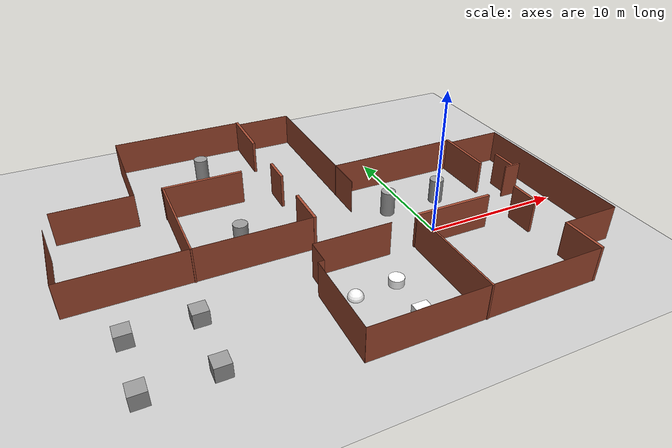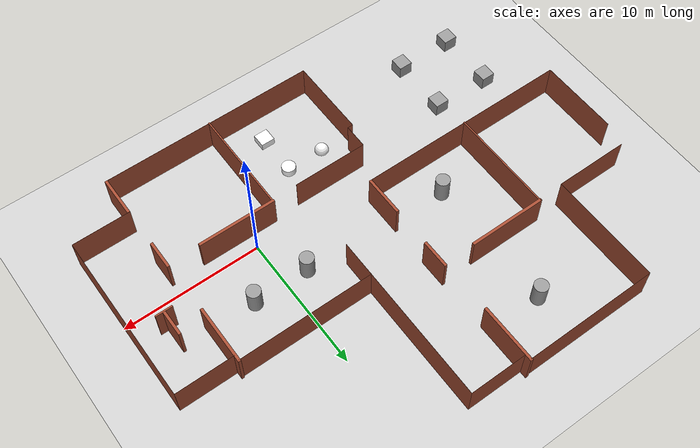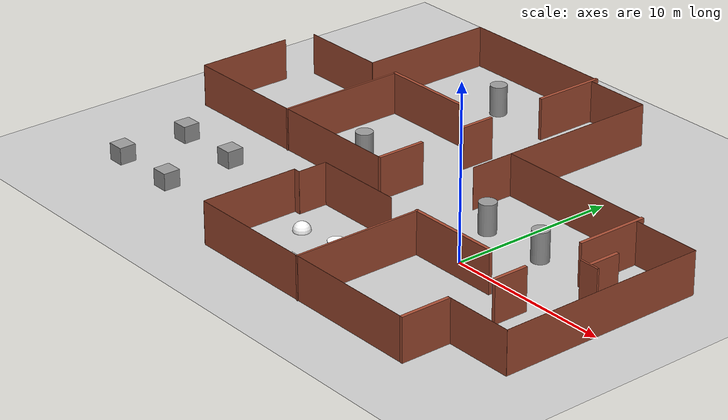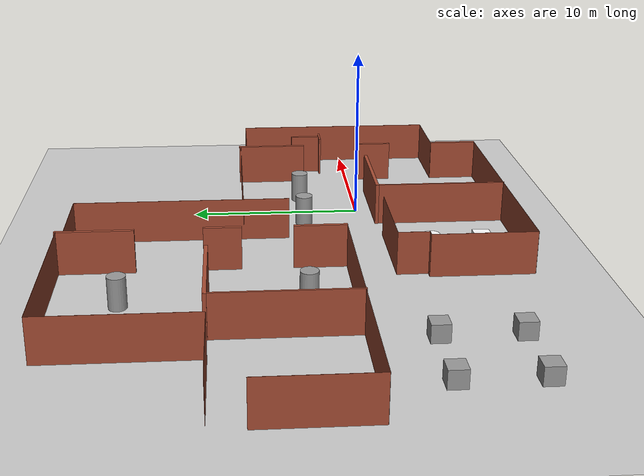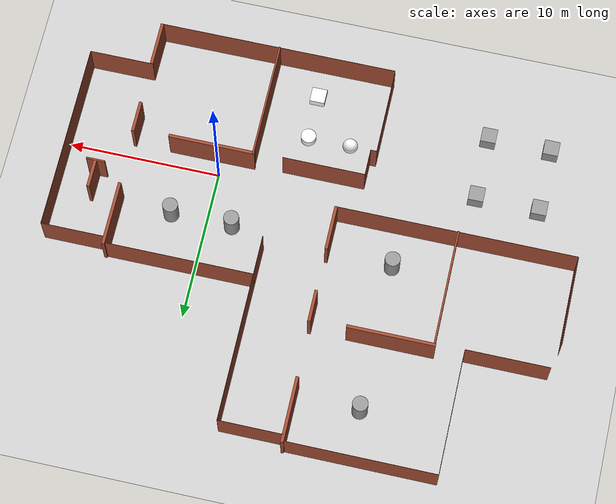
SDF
<sdf version="1.6">
 <world name="default">
  <include><uri>model://ground_plane</uri></include>
  <include><uri>model://sun</uri></include>
  <include>
   <pose>0.079097 -0.839942 0 0 -0 0</pose>
   <scale>1 1 1</scale>
   <uri>model://ANPL_Lab_Extended_0</uri>
  </include>
  <include>
   <pose>-13.886 9.34363 0 0 -0 0</pose>
   <scale>1 1 1</scale>
   <uri>model://ANPL_Lab_Extended_1</uri>
  </include>
  <include><pose>-20.8331 -1.98878 0.5 0 -0 0</pose><scale>1 1 1</scale><uri>model://unit_box</uri></include>
  <include><pose>-16.6927 -2.04585 0.5 0 -0 0</pose><scale>1 1 1</scale><uri>model://unit_box</uri></include>
  <include><pose>-20.8331 -6.27341 0.5 0 -0 0</pose><scale>1 1 1</scale><uri>model://unit_box</uri></include>
  <include><pose>-16.6927 -6.27341 0.5 0 -0 0</pose><scale>1 1 1</scale><uri>model://unit_box</uri></include>
  <include><pose>-5.12882 -5.35988 0 0 -0 0</pose><uri>model://textured_shapes_T</uri></include>
  <plugin name="gazebo_octomap" filename="librotors_gazebo_octomap_plugin.so"/>
 </world>
</sdf>

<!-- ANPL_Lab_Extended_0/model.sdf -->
<sdf version='1.6'>
  <model name='ANPL_Lab_Extended_0'>
    <link name='Wall_165'>
      <pose frame=''>-9.925 -4.975 0 0 -0 1.5708</pose>
      <self_collide>0</self_collide>
      <kinematic>0</kinematic>
      <visual name='Wall_165_Visual'>
        <pose frame=''>0 0 1.25 0 -0 0</pose>
        <geometry>
          <box>
            <size>5.86 0.01 2.5</size>
          </box>
        </geometry>
        <material>
          <script>
            <uri>file://media/materials/scripts/gazebo.material</uri>
            <name>Gazebo/Bricks</name>
          </script>
          <ambient>0.435294 0.796078 0.67451 1</ambient>
          <diffuse>1 1 1 1</diffuse>
          <specular>0.2 0.2 0.2 1</specular>
          <emissive>0 0 0 1</emissive>
        </material>
        <cast_shadows>1</cast_shadows>
        <transparency>0</transparency>
      </visual>
      <collision name='Wall_165_Collision'>
        <laser_retro>0</laser_retro>
        <max_contacts>10</max_contacts>
        <pose frame=''>0 0 1.25 0 -0 0</pose>
        <geometry>
          <box>
            <size>5.86 0.01 2.5</size>
          </box>
        </geometry>
        <surface>
          <friction>
            <ode>
              <mu>1</mu>
              <mu2>1</mu2>
              <fdir1>0 0 0</fdir1>
              <slip1>0</slip1>
              <slip2>0</slip2>
            </ode>
            <torsional>
              <coefficient>1</coefficient>
              <patch_radius>0</patch_radius>
              <surface_radius>0</surface_radius>
              <use_patch_radius>1</use_patch_radius>
              <ode>
                <slip>0</slip>
              </ode>
            </torsional>
          </friction>
          <bounce>
            <restitution_coefficient>0</restitution_coefficient>
            <threshold>1e+06</threshold>
          </bounce>
          <contact>
            <collide_without_contact>0</collide_without_contact>
            <collide_without_contact_bitmask>1</collide_without_contact_bitmask>
            <collide_bitmask>1</collide_bitmask>
            <ode>
              <soft_cfm>0</soft_cfm>
              <soft_erp>0.2</soft_erp>
              <kp>1e+13</kp>
              <kd>1</kd>
              <max_vel>0.01</max_vel>
              <min_depth>0</min_depth>
            </ode>
            <bullet>
              <split_impulse>1</split_impulse>
              <split_impulse_penetration_threshold>-0.01</split_impulse_penetration_threshold>
              <soft_cfm>0</soft_cfm>
              <soft_erp>0.2</soft_erp>
              <kp>1e+13</kp>
              <kd>1</kd>
            </bullet>
          </contact>
        </surface>
      </collision>
    </link>
    <link name='Wall_167'>
      <pose frame=''>-9.725 -2.05 0 0 -0 0</pose>
      <self_collide>0</self_collide>
      <kinematic>0</kinematic>
      <visual name='Wall_167_Visual'>
        <pose frame=''>0 0 1.25 0 -0 0</pose>
        <geometry>
          <box>
            <size>0.41 0.01 2.5</size>
          </box>
        </geometry>
        <material>
          <script>
            <uri>file://media/materials/scripts/gazebo.material</uri>
            <name>Gazebo/Bricks</name>
          </script>
          <ambient>0.435294 0.796078 0.67451 1</ambient>
          <diffuse>1 1 1 1</diffuse>
          <specular>0.2 0.2 0.2 1</specular>
          <emissive>0 0 0 1</emissive>
        </material>
        <cast_shadows>1</cast_shadows>
        <transparency>0</transparency>
      </visual>
      <collision name='Wall_167_Collision'>
        <laser_retro>0</laser_retro>
        <max_contacts>10</max_contacts>
        <pose frame=''>0 0 1.25 0 -0 0</pose>
        <geometry>
          <box>
            <size>0.41 0.01 2.5</size>
          </box>
        </geometry>
        <surface>
          <friction>
            <ode>
              <mu>1</mu>
              <mu2>1</mu2>
              <fdir1>0 0 0</fdir1>
              <slip1>0</slip1>
              <slip2>0</slip2>
            </ode>
            <torsional>
              <coefficient>1</coefficient>
              <patch_radius>0</patch_radius>
              <surface_radius>0</surface_radius>
              <use_patch_radius>1</use_patch_radius>
              <ode>
                <slip>0</slip>
              </ode>
            </torsional>
          </friction>
          <bounce>
            <restitution_coefficient>0</restitution_coefficient>
            <threshold>1e+06</threshold>
          </bounce>
          <contact>
            <collide_without_contact>0</collide_without_contact>
            <collide_without_contact_bitmask>1</collide_without_contact_bitmask>
            <collide_bitmask>1</collide_bitmask>
            <ode>
              <soft_cfm>0</soft_cfm>
              <soft_erp>0.2</soft_erp>
              <kp>1e+13</kp>
              <kd>1</kd>
              <max_vel>0.01</max_vel>
              <min_depth>0</min_depth>
            </ode>
            <bullet>
              <split_impulse>1</split_impulse>
              <split_impulse_penetration_threshold>-0.01</split_impulse_penetration_threshold>
              <soft_cfm>0</soft_cfm>
              <soft_erp>0.2</soft_erp>
              <kp>1e+13</kp>
              <kd>1</kd>
            </bullet>
          </contact>
        </surface>
      </collision>
    </link>
    <link name='Wall_169'>
      <pose frame=''>-9.525 -1.175 0 0 -0 1.5708</pose>
      <self_collide>0</self_collide>
      <kinematic>0</kinematic>
      <visual name='Wall_169_Visual'>
        <pose frame=''>0 0 1.25 0 -0 0</pose>
        <geometry>
          <box>
            <size>1.76 0.01 2.5</size>
          </box>
        </geometry>
        <material>
          <script>
            <uri>file://media/materials/scripts/gazebo.material</uri>
            <name>Gazebo/Bricks</name>
          </script>
          <ambient>0.435294 0.796078 0.67451 1</ambient>
          <diffuse>1 1 1 1</diffuse>
          <specular>0.2 0.2 0.2 1</specular>
          <emissive>0 0 0 1</emissive>
        </material>
        <cast_shadows>1</cast_shadows>
        <transparency>0</transparency>
      </visual>
      <collision name='Wall_169_Collision'>
        <laser_retro>0</laser_retro>
        <max_contacts>10</max_contacts>
        <pose frame=''>0 0 1.25 0 -0 0</pose>
        <geometry>
          <box>
            <size>1.76 0.01 2.5</size>
          </box>
        </geometry>
        <surface>
          <friction>
            <ode>
              <mu>1</mu>
              <mu2>1</mu2>
              <fdir1>0 0 0</fdir1>
              <slip1>0</slip1>
              <slip2>0</slip2>
            </ode>
            <torsional>
              <coefficient>1</coefficient>
              <patch_radius>0</patch_radius>
              <surface_radius>0</surface_radius>
              <use_patch_radius>1</use_patch_radius>
              <ode>
                <slip>0</slip>
              </ode>
            </torsional>
          </friction>
          <bounce>
            <restitution_coefficient>0</restitution_coefficient>
            <threshold>1e+06</threshold>
          </bounce>
          <contact>
            <collide_without_contact>0</collide_without_contact>
            <collide_without_contact_bitmask>1</collide_without_contact_bitmask>
            <collide_bitmask>1</collide_bitmask>
            <ode>
              <soft_cfm>0</soft_cfm>
              <soft_erp>0.2</soft_erp>
              <kp>1e+13</kp>
              <kd>1</kd>
              <max_vel>0.01</max_vel>
              <min_depth>0</min_depth>
            </ode>
            <bullet>
              <split_impulse>1</split_impulse>
              <split_impulse_penetration_threshold>-0.01</split_impulse_penetration_threshold>
              <soft_cfm>0</soft_cfm>
              <soft_erp>0.2</soft_erp>
              <kp>1e+13</kp>
              <kd>1</kd>
            </bullet>
          </contact>
        </surface>
      </collision>
    </link>
    <link name='Wall_171'>
      <pose frame=''>-6.8125 -0.3 0 0 -0 0</pose>
      <self_collide>0</self_collide>
      <kinematic>0</kinematic>
      <visual name='Wall_171_Visual'>
        <pose frame=''>0 0 1.25 0 -0 0</pose>
        <geometry>
          <box>
            <size>5.435 0.01 2.5</size>
          </box>
        </geometry>
        <material>
          <script>
            <uri>file://media/materials/scripts/gazebo.material</uri>
            <name>Gazebo/Bricks</name>
          </script>
          <ambient>0.435294 0.796078 0.67451 1</ambient>
          <diffuse>1 1 1 1</diffuse>
          <specular>0.2 0.2 0.2 1</specular>
          <emissive>0 0 0 1</emissive>
        </material>
        <cast_shadows>1</cast_shadows>
        <transparency>0</transparency>
      </visual>
      <collision name='Wall_171_Collision'>
        <laser_retro>0</laser_retro>
        <max_contacts>10</max_contacts>
        <pose frame=''>0 0 1.25 0 -0 0</pose>
        <geometry>
          <box>
            <size>5.435 0.01 2.5</size>
          </box>
        </geometry>
        <surface>
          <friction>
            <ode>
              <mu>1</mu>
              <mu2>1</mu2>
              <fdir1>0 0 0</fdir1>
              <slip1>0</slip1>
              <slip2>0</slip2>
            </ode>
            <torsional>
              <coefficient>1</coefficient>
              <patch_radius>0</patch_radius>
              <surface_radius>0</surface_radius>
              <use_patch_radius>1</use_patch_radius>
              <ode>
                <slip>0</slip>
              </ode>
            </torsional>
          </friction>
          <bounce>
            <restitution_coefficient>0</restitution_coefficient>
            <threshold>1e+06</threshold>
          </bounce>
          <contact>
            <collide_without_contact>0</collide_without_contact>
            <collide_without_contact_bitmask>1</collide_without_contact_bitmask>
            <collide_bitmask>1</collide_bitmask>
            <ode>
              <soft_cfm>0</soft_cfm>
              <soft_erp>0.2</soft_erp>
              <kp>1e+13</kp>
              <kd>1</kd>
              <max_vel>0.01</max_vel>
              <min_depth>0</min_depth>
            </ode>
            <bullet>
              <split_impulse>1</split_impulse>
              <split_impulse_penetration_threshold>-0.01</split_impulse_penetration_threshold>
              <soft_cfm>0</soft_cfm>
              <soft_erp>0.2</soft_erp>
              <kp>1e+13</kp>
              <kd>1</kd>
            </bullet>
          </contact>
        </surface>
      </collision>
    </link>
    <link name='Wall_175'>
      <pose frame=''>0.7875 7.9 0 0 -0 0</pose>
      <self_collide>0</self_collide>
      <kinematic>0</kinematic>
      <visual name='Wall_175_Visual'>
        <pose frame=''>0 0 1.25 0 -0 0</pose>
        <geometry>
          <box>
            <size>9.785 0.01 2.5</size>
          </box>
        </geometry>
        <material>
          <script>
            <uri>file://media/materials/scripts/gazebo.material</uri>
            <name>Gazebo/Bricks</name>
          </script>
          <ambient>0.435294 0.796078 0.67451 1</ambient>
          <diffuse>1 1 1 1</diffuse>
          <specular>0.2 0.2 0.2 1</specular>
          <emissive>0 0 0 1</emissive>
        </material>
        <cast_shadows>1</cast_shadows>
        <transparency>0</transparency>
      </visual>
      <collision name='Wall_175_Collision'>
        <laser_retro>0</laser_retro>
        <max_contacts>10</max_contacts>
        <pose frame=''>0 0 1.25 0 -0 0</pose>
        <geometry>
          <box>
            <size>9.785 0.01 2.5</size>
          </box>
        </geometry>
        <surface>
          <friction>
            <ode>
              <mu>1</mu>
              <mu2>1</mu2>
              <fdir1>0 0 0</fdir1>
              <slip1>0</slip1>
              <slip2>0</slip2>
            </ode>
            <torsional>
              <coefficient>1</coefficient>
              <patch_radius>0</patch_radius>
              <surface_radius>0</surface_radius>
              <use_patch_radius>1</use_patch_radius>
              <ode>
                <slip>0</slip>
              </ode>
            </torsional>
          </friction>
          <bounce>
            <restitution_coefficient>0</restitution_coefficient>
            <threshold>1e+06</threshold>
          </bounce>
          <contact>
            <collide_without_contact>0</collide_without_contact>
            <collide_without_contact_bitmask>1</collide_without_contact_bitmask>
            <collide_bitmask>1</collide_bitmask>
            <ode>
              <soft_cfm>0</soft_cfm>
              <soft_erp>0.2</soft_erp>
              <kp>1e+13</kp>
              <kd>1</kd>
              <max_vel>0.01</max_vel>
              <min_depth>0</min_depth>
            </ode>
            <bullet>
              <split_impulse>1</split_impulse>
              <split_impulse_penetration_threshold>-0.01</split_impulse_penetration_threshold>
              <soft_cfm>0</soft_cfm>
              <soft_erp>0.2</soft_erp>
              <kp>1e+13</kp>
              <kd>1</kd>
            </bullet>
          </contact>
        </surface>
      </collision>
    </link>
    <link name='Wall_177'>
      <pose frame=''>5.675 5.85 0 0 0 -1.5708</pose>
      <self_collide>0</self_collide>
      <kinematic>0</kinematic>
      <visual name='Wall_177_Visual'>
        <pose frame=''>0 0 1.25 0 -0 0</pose>
        <geometry>
          <box>
            <size>4.3 0.2 2.5</size>
          </box>
        </geometry>
        <material>
          <script>
            <uri>file://media/materials/scripts/gazebo.material</uri>
            <name>Gazebo/Bricks</name>
          </script>
          <ambient>0.435294 0.796078 0.67451 1</ambient>
          <diffuse>1 1 1 1</diffuse>
          <specular>0.2 0.2 0.2 1</specular>
          <emissive>0 0 0 1</emissive>
        </material>
        <cast_shadows>1</cast_shadows>
        <transparency>0</transparency>
      </visual>
      <collision name='Wall_177_Collision'>
        <laser_retro>0</laser_retro>
        <max_contacts>10</max_contacts>
        <pose frame=''>0 0 1.25 0 -0 0</pose>
        <geometry>
          <box>
            <size>4.3 0.2 2.5</size>
          </box>
        </geometry>
        <surface>
          <friction>
            <ode>
              <mu>1</mu>
              <mu2>1</mu2>
              <fdir1>0 0 0</fdir1>
              <slip1>0</slip1>
              <slip2>0</slip2>
            </ode>
            <torsional>
              <coefficient>1</coefficient>
              <patch_radius>0</patch_radius>
              <surface_radius>0</surface_radius>
              <use_patch_radius>1</use_patch_radius>
              <ode>
                <slip>0</slip>
              </ode>
            </torsional>
          </friction>
          <bounce>
            <restitution_coefficient>0</restitution_coefficient>
            <threshold>1e+06</threshold>
          </bounce>
          <contact>
            <collide_without_contact>0</collide_without_contact>
            <collide_without_contact_bitmask>1</collide_without_contact_bitmask>
            <collide_bitmask>1</collide_bitmask>
            <ode>
              <soft_cfm>0</soft_cfm>
              <soft_erp>0.2</soft_erp>
              <kp>1e+13</kp>
              <kd>1</kd>
              <max_vel>0.01</max_vel>
              <min_depth>0</min_depth>
            </ode>
            <bullet>
              <split_impulse>1</split_impulse>
              <split_impulse_penetration_threshold>-0.01</split_impulse_penetration_threshold>
              <soft_cfm>0</soft_cfm>
              <soft_erp>0.2</soft_erp>
              <kp>1e+13</kp>
              <kd>1</kd>
            </bullet>
          </contact>
        </surface>
      </collision>
    </link>
    <link name='Wall_179'>
      <pose frame=''>7.775 7.5 0 0 -0 0</pose>
      <self_collide>0</self_collide>
      <kinematic>0</kinematic>
      <visual name='Wall_179_Visual'>
        <pose frame=''>0 0 1.25 0 -0 0</pose>
        <geometry>
          <box>
            <size>4.21 0.01 2.5</size>
          </box>
        </geometry>
        <material>
          <script>
            <uri>file://media/materials/scripts/gazebo.material</uri>
            <name>Gazebo/Bricks</name>
          </script>
          <ambient>0.435294 0.796078 0.67451 1</ambient>
          <diffuse>1 1 1 1</diffuse>
          <specular>0.2 0.2 0.2 1</specular>
          <emissive>0 0 0 1</emissive>
        </material>
        <cast_shadows>1</cast_shadows>
        <transparency>0</transparency>
      </visual>
      <collision name='Wall_179_Collision'>
        <laser_retro>0</laser_retro>
        <max_contacts>10</max_contacts>
        <pose frame=''>0 0 1.25 0 -0 0</pose>
        <geometry>
          <box>
            <size>4.21 0.01 2.5</size>
          </box>
        </geometry>
        <surface>
          <friction>
            <ode>
              <mu>1</mu>
              <mu2>1</mu2>
              <fdir1>0 0 0</fdir1>
              <slip1>0</slip1>
              <slip2>0</slip2>
            </ode>
            <torsional>
              <coefficient>1</coefficient>
              <patch_radius>0</patch_radius>
              <surface_radius>0</surface_radius>
              <use_patch_radius>1</use_patch_radius>
              <ode>
                <slip>0</slip>
              </ode>
            </torsional>
          </friction>
          <bounce>
            <restitution_coefficient>0</restitution_coefficient>
            <threshold>1e+06</threshold>
          </bounce>
          <contact>
            <collide_without_contact>0</collide_without_contact>
            <collide_without_contact_bitmask>1</collide_without_contact_bitmask>
            <collide_bitmask>1</collide_bitmask>
            <ode>
              <soft_cfm>0</soft_cfm>
              <soft_erp>0.2</soft_erp>
              <kp>1e+13</kp>
              <kd>1</kd>
              <max_vel>0.01</max_vel>
              <min_depth>0</min_depth>
            </ode>
            <bullet>
              <split_impulse>1</split_impulse>
              <split_impulse_penetration_threshold>-0.01</split_impulse_penetration_threshold>
              <soft_cfm>0</soft_cfm>
              <soft_erp>0.2</soft_erp>
              <kp>1e+13</kp>
              <kd>1</kd>
            </bullet>
          </contact>
        </surface>
      </collision>
    </link>
    <link name='Wall_181'>
      <pose frame=''>9.875 1.285 0 0 0 -1.5708</pose>
      <self_collide>0</self_collide>
      <kinematic>0</kinematic>
      <visual name='Wall_181_Visual'>
        <pose frame=''>0 0 1.25 0 -0 0</pose>
        <geometry>
          <box>
            <size>12.44 0.01 2.5</size>
          </box>
        </geometry>
        <material>
          <script>
            <uri>file://media/materials/scripts/gazebo.material</uri>
            <name>Gazebo/Bricks</name>
          </script>
          <ambient>0.435294 0.796078 0.67451 1</ambient>
          <diffuse>1 1 1 1</diffuse>
          <specular>0.2 0.2 0.2 1</specular>
          <emissive>0 0 0 1</emissive>
        </material>
        <cast_shadows>1</cast_shadows>
        <transparency>0</transparency>
      </visual>
      <collision name='Wall_181_Collision'>
        <laser_retro>0</laser_retro>
        <max_contacts>10</max_contacts>
        <pose frame=''>0 0 1.25 0 -0 0</pose>
        <geometry>
          <box>
            <size>12.44 0.01 2.5</size>
          </box>
        </geometry>
        <surface>
          <friction>
            <ode>
              <mu>1</mu>
              <mu2>1</mu2>
              <fdir1>0 0 0</fdir1>
              <slip1>0</slip1>
              <slip2>0</slip2>
            </ode>
            <torsional>
              <coefficient>1</coefficient>
              <patch_radius>0</patch_radius>
              <surface_radius>0</surface_radius>
              <use_patch_radius>1</use_patch_radius>
              <ode>
                <slip>0</slip>
              </ode>
            </torsional>
          </friction>
          <bounce>
            <restitution_coefficient>0</restitution_coefficient>
            <threshold>1e+06</threshold>
          </bounce>
          <contact>
            <collide_without_contact>0</collide_without_contact>
            <collide_without_contact_bitmask>1</collide_without_contact_bitmask>
            <collide_bitmask>1</collide_bitmask>
            <ode>
              <soft_cfm>0</soft_cfm>
              <soft_erp>0.2</soft_erp>
              <kp>1e+13</kp>
              <kd>1</kd>
              <max_vel>0.01</max_vel>
              <min_depth>0</min_depth>
            </ode>
            <bullet>
              <split_impulse>1</split_impulse>
              <split_impulse_penetration_threshold>-0.01</split_impulse_penetration_threshold>
              <soft_cfm>0</soft_cfm>
              <soft_erp>0.2</soft_erp>
              <kp>1e+13</kp>
              <kd>1</kd>
            </bullet>
          </contact>
        </surface>
      </collision>
    </link>
    <link name='Wall_183'>
      <pose frame=''>7.6044 3.46126 0 0 -0 1.5708</pose>
      <inertial>
        <mass>1.43571</mass>
        <pose frame=''>0 0 0 0 -0 0</pose>
        <inertia>
          <ixx>1.43571</ixx>
          <ixy>0</ixy>
          <ixz>0</ixz>
          <iyy>2.19753</iyy>
          <iyz>0</iyz>
          <izz>2.19753</izz>
        </inertia>
      </inertial>
      <self_collide>0</self_collide>
      <kinematic>0</kinematic>
      <visual name='Wall_183_Visual'>
        <pose frame=''>0 0 1.25 0 -0 0</pose>
        <geometry>
          <box>
            <size>1.86641 0.2 2.5</size>
          </box>
        </geometry>
        <material>
          <script>
            <uri>file://media/materials/scripts/gazebo.material</uri>
            <name>Gazebo/Bricks</name>
          </script>
          <ambient>0.435 0.796 0.675 1</ambient>
          <diffuse>1 1 1 1</diffuse>
          <specular>0.2 0.2 0.2 1</specular>
          <emissive>0 0 0 1</emissive>
          <shader type='vertex'>
            <normal_map>__default__</normal_map>
          </shader>
        </material>
        <cast_shadows>1</cast_shadows>
        <transparency>0</transparency>
      </visual>
      <collision name='Wall_183_Collision'>
        <laser_retro>0</laser_retro>
        <max_contacts>10</max_contacts>
        <pose frame=''>0 0 1.25 0 -0 0</pose>
        <geometry>
          <box>
            <size>1.86641 0.2 2.5</size>
          </box>
        </geometry>
        <surface>
          <friction>
            <ode>
              <mu>1</mu>
              <mu2>1</mu2>
              <fdir1>0 0 0</fdir1>
              <slip1>0</slip1>
              <slip2>0</slip2>
            </ode>
            <torsional>
              <coefficient>1</coefficient>
              <patch_radius>0</patch_radius>
              <surface_radius>0</surface_radius>
              <use_patch_radius>1</use_patch_radius>
              <ode>
                <slip>0</slip>
              </ode>
            </torsional>
          </friction>
          <bounce>
            <restitution_coefficient>0</restitution_coefficient>
            <threshold>1e+06</threshold>
          </bounce>
          <contact>
            <collide_without_contact>0</collide_without_contact>
            <collide_without_contact_bitmask>1</collide_without_contact_bitmask>
            <collide_bitmask>1</collide_bitmask>
            <ode>
              <soft_cfm>0</soft_cfm>
              <soft_erp>0.2</soft_erp>
              <kp>1e+13</kp>
              <kd>1</kd>
              <max_vel>0.01</max_vel>
              <min_depth>0</min_depth>
            </ode>
            <bullet>
              <split_impulse>1</split_impulse>
              <split_impulse_penetration_threshold>-0.01</split_impulse_penetration_threshold>
              <soft_cfm>0</soft_cfm>
              <soft_erp>0.2</soft_erp>
              <kp>1e+13</kp>
              <kd>1</kd>
            </bullet>
          </contact>
        </surface>
      </collision>
    </link>
    <link name='Wall_185'>
      <pose frame=''>5.76868 -1.05 0 0 0 -1.5708</pose>
      <inertial>
        <mass>1</mass>
        <pose frame=''>0 0 0 0 -0 0</pose>
        <inertia>
          <ixx>1</ixx>
          <ixy>0</ixy>
          <ixz>0</ixz>
          <iyy>1</iyy>
          <iyz>0</iyz>
          <izz>1</izz>
        </inertia>
      </inertial>
      <self_collide>0</self_collide>
      <kinematic>0</kinematic>
      <visual name='Wall_185_Visual'>
        <pose frame=''>0 0 1.25 0 -0 0</pose>
        <geometry>
          <box>
            <size>2.1 0.2 2.5</size>
          </box>
        </geometry>
        <material>
          <script>
            <uri>file://media/materials/scripts/gazebo.material</uri>
            <name>Gazebo/Bricks</name>
          </script>
          <ambient>0.435 0.796 0.675 1</ambient>
          <diffuse>1 1 1 1</diffuse>
          <specular>0.2 0.2 0.2 1</specular>
          <emissive>0 0 0 1</emissive>
          <shader type='vertex'>
            <normal_map>__default__</normal_map>
          </shader>
        </material>
        <cast_shadows>1</cast_shadows>
        <transparency>0</transparency>
      </visual>
      <collision name='Wall_185_Collision'>
        <laser_retro>0</laser_retro>
        <max_contacts>10</max_contacts>
        <pose frame=''>0 0 1.25 0 -0 0</pose>
        <geometry>
          <box>
            <size>2.1 0.2 2.5</size>
          </box>
        </geometry>
        <surface>
          <friction>
            <ode>
              <mu>1</mu>
              <mu2>1</mu2>
              <fdir1>0 0 0</fdir1>
              <slip1>0</slip1>
              <slip2>0</slip2>
            </ode>
            <torsional>
              <coefficient>1</coefficient>
              <patch_radius>0</patch_radius>
              <surface_radius>0</surface_radius>
              <use_patch_radius>1</use_patch_radius>
              <ode>
                <slip>0</slip>
              </ode>
            </torsional>
          </friction>
          <bounce>
            <restitution_coefficient>0</restitution_coefficient>
            <threshold>1e+06</threshold>
          </bounce>
          <contact>
            <collide_without_contact>0</collide_without_contact>
            <collide_without_contact_bitmask>1</collide_without_contact_bitmask>
            <collide_bitmask>1</collide_bitmask>
            <ode>
              <soft_cfm>0</soft_cfm>
              <soft_erp>0.2</soft_erp>
              <kp>1e+13</kp>
              <kd>1</kd>
              <max_vel>0.01</max_vel>
              <min_depth>0</min_depth>
            </ode>
            <bullet>
              <split_impulse>1</split_impulse>
              <split_impulse_penetration_threshold>-0.01</split_impulse_penetration_threshold>
              <soft_cfm>0</soft_cfm>
              <soft_erp>0.2</soft_erp>
              <kp>1e+13</kp>
              <kd>1</kd>
            </bullet>
          </contact>
        </surface>
      </collision>
    </link>
    <link name='Wall_187'>
      <pose frame=''>7.59405 2.49 0 0 -0 0</pose>
      <inertial>
        <inertia>
          <ixx>nan</ixx>
          <ixy>0</ixy>
          <ixz>0</ixz>
          <iyy>nan</iyy>
          <iyz>0</iyz>
          <izz>nan</izz>
        </inertia>
        <mass>0</mass>
        <pose frame=''>0 0 0 0 -0 0</pose>
      </inertial>
      <self_collide>0</self_collide>
      <kinematic>0</kinematic>
      <visual name='Wall_187_Visual'>
        <pose frame=''>0 0 1.25 0 -0 0</pose>
        <geometry>
          <box>
            <size>1.23163 0.11 2.5</size>
          </box>
        </geometry>
        <material>
          <script>
            <uri>file://media/materials/scripts/gazebo.material</uri>
            <name>Gazebo/Bricks</name>
          </script>
          <ambient>0.435294 0.796078 0.67451 1</ambient>
          <diffuse>1 1 1 1</diffuse>
          <specular>0.2 0.2 0.2 1</specular>
          <emissive>0 0 0 1</emissive>
        </material>
        <cast_shadows>1</cast_shadows>
        <transparency>0</transparency>
      </visual>
      <collision name='Wall_187_Collision'>
        <laser_retro>0</laser_retro>
        <max_contacts>10</max_contacts>
        <pose frame=''>0 0 1.25 0 -0 0</pose>
        <geometry>
          <box>
            <size>1.23163 0.11 2.5</size>
          </box>
        </geometry>
        <surface>
          <friction>
            <ode>
              <mu>1</mu>
              <mu2>1</mu2>
              <fdir1>0 0 0</fdir1>
              <slip1>0</slip1>
              <slip2>0</slip2>
            </ode>
            <torsional>
              <coefficient>1</coefficient>
              <patch_radius>0</patch_radius>
              <surface_radius>0</surface_radius>
              <use_patch_radius>1</use_patch_radius>
              <ode>
                <slip>0</slip>
              </ode>
            </torsional>
          </friction>
          <bounce>
            <restitution_coefficient>0</restitution_coefficient>
            <threshold>1e+06</threshold>
          </bounce>
          <contact>
            <collide_without_contact>0</collide_without_contact>
            <collide_without_contact_bitmask>1</collide_without_contact_bitmask>
            <collide_bitmask>1</collide_bitmask>
            <ode>
              <soft_cfm>0</soft_cfm>
              <soft_erp>0.2</soft_erp>
              <kp>1e+13</kp>
              <kd>1</kd>
              <max_vel>0.01</max_vel>
              <min_depth>0</min_depth>
            </ode>
            <bullet>
              <split_impulse>1</split_impulse>
              <split_impulse_penetration_threshold>-0.01</split_impulse_penetration_threshold>
              <soft_cfm>0</soft_cfm>
              <soft_erp>0.2</soft_erp>
              <kp>1e+13</kp>
              <kd>1</kd>
            </bullet>
          </contact>
        </surface>
      </collision>
    </link>
    <link name='Wall_201'>
      <pose frame=''>7.775 -4.93 0 0 -0 3.14159</pose>
      <self_collide>0</self_collide>
      <kinematic>0</kinematic>
      <visual name='Wall_201_Visual'>
        <pose frame=''>0 0 1.25 0 -0 0</pose>
        <geometry>
          <box>
            <size>4.21 0.01 2.5</size>
          </box>
        </geometry>
        <material>
          <script>
            <uri>file://media/materials/scripts/gazebo.material</uri>
            <name>Gazebo/Bricks</name>
          </script>
          <ambient>0.435294 0.796078 0.67451 1</ambient>
          <diffuse>1 1 1 1</diffuse>
          <specular>0.2 0.2 0.2 1</specular>
          <emissive>0 0 0 1</emissive>
        </material>
        <cast_shadows>1</cast_shadows>
        <transparency>0</transparency>
      </visual>
      <collision name='Wall_201_Collision'>
        <laser_retro>0</laser_retro>
        <max_contacts>10</max_contacts>
        <pose frame=''>0 0 1.25 0 -0 0</pose>
        <geometry>
          <box>
            <size>4.21 0.01 2.5</size>
          </box>
        </geometry>
        <surface>
          <friction>
            <ode>
              <mu>1</mu>
              <mu2>1</mu2>
              <fdir1>0 0 0</fdir1>
              <slip1>0</slip1>
              <slip2>0</slip2>
            </ode>
            <torsional>
              <coefficient>1</coefficient>
              <patch_radius>0</patch_radius>
              <surface_radius>0</surface_radius>
              <use_patch_radius>1</use_patch_radius>
              <ode>
                <slip>0</slip>
              </ode>
            </torsional>
          </friction>
          <bounce>
            <restitution_coefficient>0</restitution_coefficient>
            <threshold>1e+06</threshold>
          </bounce>
          <contact>
            <collide_without_contact>0</collide_without_contact>
            <collide_without_contact_bitmask>1</collide_without_contact_bitmask>
            <collide_bitmask>1</collide_bitmask>
            <ode>
              <soft_cfm>0</soft_cfm>
              <soft_erp>0.2</soft_erp>
              <kp>1e+13</kp>
              <kd>1</kd>
              <max_vel>0.01</max_vel>
              <min_depth>0</min_depth>
            </ode>
            <bullet>
              <split_impulse>1</split_impulse>
              <split_impulse_penetration_threshold>-0.01</split_impulse_penetration_threshold>
              <soft_cfm>0</soft_cfm>
              <soft_erp>0.2</soft_erp>
              <kp>1e+13</kp>
              <kd>1</kd>
            </bullet>
          </contact>
        </surface>
      </collision>
    </link>
    <link name='Wall_203'>
      <pose frame=''>5.76868 -6.42951 0 0 0 -1.5708</pose>
      <inertial>
        <inertia>
          <ixx>1.79769e+308</ixx>
          <ixy>0</ixy>
          <ixz>0</ixz>
          <iyy>1.79769e+308</iyy>
          <iyz>0</iyz>
          <izz>1.79769e+308</izz>
        </inertia>
        <mass>0</mass>
        <pose frame=''>0 0 0 0 -0 0</pose>
      </inertial>
      <self_collide>0</self_collide>
      <kinematic>0</kinematic>
      <visual name='Wall_203_Visual'>
        <pose frame=''>0 0 1.25 0 -0 0</pose>
        <geometry>
          <box>
            <size>2.97075 0.2 2.5</size>
          </box>
        </geometry>
        <material>
          <script>
            <uri>file://media/materials/scripts/gazebo.material</uri>
            <name>Gazebo/Bricks</name>
          </script>
          <ambient>0.435 0.796 0.675 1</ambient>
          <diffuse>1 1 1 1</diffuse>
          <specular>0.2 0.2 0.2 1</specular>
          <emissive>0 0 0 1</emissive>
          <shader type='vertex'>
            <normal_map>__default__</normal_map>
          </shader>
        </material>
        <cast_shadows>1</cast_shadows>
        <transparency>0</transparency>
      </visual>
      <collision name='Wall_203_Collision'>
        <laser_retro>0</laser_retro>
        <max_contacts>10</max_contacts>
        <pose frame=''>0 0 1.25 0 -0 0</pose>
        <geometry>
          <box>
            <size>2.97075 0.2 2.5</size>
          </box>
        </geometry>
        <surface>
          <friction>
            <ode>
              <mu>1</mu>
              <mu2>1</mu2>
              <fdir1>0 0 0</fdir1>
              <slip1>0</slip1>
              <slip2>0</slip2>
            </ode>
            <torsional>
              <coefficient>1</coefficient>
              <patch_radius>0</patch_radius>
              <surface_radius>0</surface_radius>
              <use_patch_radius>1</use_patch_radius>
              <ode>
                <slip>0</slip>
              </ode>
            </torsional>
          </friction>
          <bounce>
            <restitution_coefficient>0</restitution_coefficient>
            <threshold>1e+06</threshold>
          </bounce>
          <contact>
            <collide_without_contact>0</collide_without_contact>
            <collide_without_contact_bitmask>1</collide_without_contact_bitmask>
            <collide_bitmask>1</collide_bitmask>
            <ode>
              <soft_cfm>0</soft_cfm>
              <soft_erp>0.2</soft_erp>
              <kp>1e+13</kp>
              <kd>1</kd>
              <max_vel>0.01</max_vel>
              <min_depth>0</min_depth>
            </ode>
            <bullet>
              <split_impulse>1</split_impulse>
              <split_impulse_penetration_threshold>-0.01</split_impulse_penetration_threshold>
              <soft_cfm>0</soft_cfm>
              <soft_erp>0.2</soft_erp>
              <kp>1e+13</kp>
              <kd>1</kd>
            </bullet>
          </contact>
        </surface>
      </collision>
    </link>
    <link name='Wall_205'>
      <pose frame=''>-2.125 -7.9 0 0 -0 3.14159</pose>
      <self_collide>0</self_collide>
      <kinematic>0</kinematic>
      <visual name='Wall_205_Visual'>
        <pose frame=''>0 0 1.25 0 -0 0</pose>
        <geometry>
          <box>
            <size>15.61 0.01 2.5</size>
          </box>
        </geometry>
        <material>
          <script>
            <uri>file://media/materials/scripts/gazebo.material</uri>
            <name>Gazebo/Bricks</name>
          </script>
          <ambient>0.435294 0.796078 0.67451 1</ambient>
          <diffuse>1 1 1 1</diffuse>
          <specular>0.2 0.2 0.2 1</specular>
          <emissive>0 0 0 1</emissive>
        </material>
        <cast_shadows>1</cast_shadows>
        <transparency>0</transparency>
      </visual>
      <collision name='Wall_205_Collision'>
        <laser_retro>0</laser_retro>
        <max_contacts>10</max_contacts>
        <pose frame=''>0 0 1.25 0 -0 0</pose>
        <geometry>
          <box>
            <size>15.61 0.01 2.5</size>
          </box>
        </geometry>
        <surface>
          <friction>
            <ode>
              <mu>1</mu>
              <mu2>1</mu2>
              <fdir1>0 0 0</fdir1>
              <slip1>0</slip1>
              <slip2>0</slip2>
            </ode>
            <torsional>
              <coefficient>1</coefficient>
              <patch_radius>0</patch_radius>
              <surface_radius>0</surface_radius>
              <use_patch_radius>1</use_patch_radius>
              <ode>
                <slip>0</slip>
              </ode>
            </torsional>
          </friction>
          <bounce>
            <restitution_coefficient>0</restitution_coefficient>
            <threshold>1e+06</threshold>
          </bounce>
          <contact>
            <collide_without_contact>0</collide_without_contact>
            <collide_without_contact_bitmask>1</collide_without_contact_bitmask>
            <collide_bitmask>1</collide_bitmask>
            <ode>
              <soft_cfm>0</soft_cfm>
              <soft_erp>0.2</soft_erp>
              <kp>1e+13</kp>
              <kd>1</kd>
              <max_vel>0.01</max_vel>
              <min_depth>0</min_depth>
            </ode>
            <bullet>
              <split_impulse>1</split_impulse>
              <split_impulse_penetration_threshold>-0.01</split_impulse_penetration_threshold>
              <soft_cfm>0</soft_cfm>
              <soft_erp>0.2</soft_erp>
              <kp>1e+13</kp>
              <kd>1</kd>
            </bullet>
          </contact>
        </surface>
      </collision>
    </link>
    <link name='Wall_207'>
      <pose frame=''>-2.175 -4.05 0 0 -0 1.5708</pose>
      <self_collide>0</self_collide>
      <kinematic>0</kinematic>
      <visual name='Wall_207_Visual'>
        <pose frame=''>0 0 1.25 0 -0 0</pose>
        <geometry>
          <box>
            <size>7.81 0.11 2.5</size>
          </box>
        </geometry>
        <material>
          <script>
            <uri>file://media/materials/scripts/gazebo.material</uri>
            <name>Gazebo/Bricks</name>
          </script>
          <ambient>0.435294 0.796078 0.67451 1</ambient>
          <diffuse>1 1 1 1</diffuse>
          <specular>0.2 0.2 0.2 1</specular>
          <emissive>0 0 0 1</emissive>
        </material>
        <cast_shadows>1</cast_shadows>
        <transparency>0</transparency>
      </visual>
      <collision name='Wall_207_Collision'>
        <laser_retro>0</laser_retro>
        <max_contacts>10</max_contacts>
        <pose frame=''>0 0 1.25 0 -0 0</pose>
        <geometry>
          <box>
            <size>7.81 0.11 2.5</size>
          </box>
        </geometry>
        <surface>
          <friction>
            <ode>
              <mu>1</mu>
              <mu2>1</mu2>
              <fdir1>0 0 0</fdir1>
              <slip1>0</slip1>
              <slip2>0</slip2>
            </ode>
            <torsional>
              <coefficient>1</coefficient>
              <patch_radius>0</patch_radius>
              <surface_radius>0</surface_radius>
              <use_patch_radius>1</use_patch_radius>
              <ode>
                <slip>0</slip>
              </ode>
            </torsional>
          </friction>
          <bounce>
            <restitution_coefficient>0</restitution_coefficient>
            <threshold>1e+06</threshold>
          </bounce>
          <contact>
            <collide_without_contact>0</collide_without_contact>
            <collide_without_contact_bitmask>1</collide_without_contact_bitmask>
            <collide_bitmask>1</collide_bitmask>
            <ode>
              <soft_cfm>0</soft_cfm>
              <soft_erp>0.2</soft_erp>
              <kp>1e+13</kp>
              <kd>1</kd>
              <max_vel>0.01</max_vel>
              <min_depth>0</min_depth>
            </ode>
            <bullet>
              <split_impulse>1</split_impulse>
              <split_impulse_penetration_threshold>-0.01</split_impulse_penetration_threshold>
              <soft_cfm>0</soft_cfm>
              <soft_erp>0.2</soft_erp>
              <kp>1e+13</kp>
              <kd>1</kd>
            </bullet>
          </contact>
        </surface>
      </collision>
    </link>
    <link name='Wall_209'>
      <pose frame=''>0.571 -0.2 0 0 -0 0</pose>
      <inertial>
        <mass>1</mass>
        <pose frame=''>0 0 0 0 -0 0</pose>
        <inertia>
          <ixx>1</ixx>
          <ixy>0</ixy>
          <ixz>0</ixz>
          <iyy>1</iyy>
          <iyz>0</iyz>
          <izz>1</izz>
        </inertia>
      </inertial>
      <self_collide>0</self_collide>
      <kinematic>0</kinematic>
      <visual name='Wall_209_Visual'>
        <pose frame=''>0 0 1.25 0 -0 0</pose>
        <geometry>
          <box>
            <size>5.692 0.2 2.5</size>
          </box>
        </geometry>
        <material>
          <script>
            <uri>file://media/materials/scripts/gazebo.material</uri>
            <name>Gazebo/Bricks</name>
          </script>
          <ambient>0.435 0.796 0.675 1</ambient>
          <diffuse>1 1 1 1</diffuse>
          <specular>0.2 0.2 0.2 1</specular>
          <emissive>0 0 0 1</emissive>
          <shader type='vertex'>
            <normal_map>__default__</normal_map>
          </shader>
        </material>
        <cast_shadows>1</cast_shadows>
        <transparency>0</transparency>
      </visual>
      <collision name='Wall_209_Collision'>
        <laser_retro>0</laser_retro>
        <max_contacts>10</max_contacts>
        <pose frame=''>0 0 1.25 0 -0 0</pose>
        <geometry>
          <box>
            <size>5.692 0.2 2.5</size>
          </box>
        </geometry>
        <surface>
          <friction>
            <ode>
              <mu>1</mu>
              <mu2>1</mu2>
              <fdir1>0 0 0</fdir1>
              <slip1>0</slip1>
              <slip2>0</slip2>
            </ode>
            <torsional>
              <coefficient>1</coefficient>
              <patch_radius>0</patch_radius>
              <surface_radius>0</surface_radius>
              <use_patch_radius>1</use_patch_radius>
              <ode>
                <slip>0</slip>
              </ode>
            </torsional>
          </friction>
          <bounce>
            <restitution_coefficient>0</restitution_coefficient>
            <threshold>1e+06</threshold>
          </bounce>
          <contact>
            <collide_without_contact>0</collide_without_contact>
            <collide_without_contact_bitmask>1</collide_without_contact_bitmask>
            <collide_bitmask>1</collide_bitmask>
            <ode>
              <soft_cfm>0</soft_cfm>
              <soft_erp>0.2</soft_erp>
              <kp>1e+13</kp>
              <kd>1</kd>
              <max_vel>0.01</max_vel>
              <min_depth>0</min_depth>
            </ode>
            <bullet>
              <split_impulse>1</split_impulse>
              <split_impulse_penetration_threshold>-0.01</split_impulse_penetration_threshold>
              <soft_cfm>0</soft_cfm>
              <soft_erp>0.2</soft_erp>
              <kp>1e+13</kp>
              <kd>1</kd>
            </bullet>
          </contact>
        </surface>
      </collision>
    </link>
    <link name='link_0'>
      <pose frame=''>2.28416 4.2 0.5 0 -0 0</pose>
      <inertial>
        <mass>1</mass>
        <inertia>
          <ixx>0.145833</ixx>
          <ixy>0</ixy>
          <ixz>0</ixz>
          <iyy>0.145833</iyy>
          <iyz>0</iyz>
          <izz>0.125</izz>
        </inertia>
        <pose frame=''>0 0 0 0 -0 0</pose>
      </inertial>
      <self_collide>0</self_collide>
      <kinematic>0</kinematic>
      <visual name='visual'>
        <pose frame=''>0 0 0 0 -0 0</pose>
        <geometry>
          <cylinder>
            <radius>0.5</radius>
            <length>2.5</length>
          </cylinder>
        </geometry>
        <material>
          <lighting>1</lighting>
          <script>
            <uri>file://media/materials/scripts/gazebo.material</uri>
            <name>Gazebo/Grey</name>
          </script>
          <ambient>0.3 0.3 0.3 1</ambient>
          <diffuse>0.7 0.7 0.7 1</diffuse>
          <specular>0.01 0.01 0.01 1</specular>
          <emissive>0 0 0 1</emissive>
          <shader type='vertex'>
            <normal_map>__default__</normal_map>
          </shader>
        </material>
        <cast_shadows>1</cast_shadows>
        <transparency>0</transparency>
      </visual>
      <collision name='collision'>
        <laser_retro>0</laser_retro>
        <max_contacts>10</max_contacts>
        <pose frame=''>0 0 0 0 -0 0</pose>
        <geometry>
          <cylinder>
            <radius>0.5</radius>
            <length>2.5</length>
          </cylinder>
        </geometry>
        <surface>
          <friction>
            <ode>
              <mu>1</mu>
              <mu2>1</mu2>
              <fdir1>0 0 0</fdir1>
              <slip1>0</slip1>
              <slip2>0</slip2>
            </ode>
            <torsional>
              <coefficient>1</coefficient>
              <patch_radius>0</patch_radius>
              <surface_radius>0</surface_radius>
              <use_patch_radius>1</use_patch_radius>
              <ode>
                <slip>0</slip>
              </ode>
            </torsional>
          </friction>
          <bounce>
            <restitution_coefficient>0</restitution_coefficient>
            <threshold>1e+06</threshold>
          </bounce>
          <contact>
            <collide_without_contact>0</collide_without_contact>
            <collide_without_contact_bitmask>1</collide_without_contact_bitmask>
            <collide_bitmask>1</collide_bitmask>
            <ode>
              <soft_cfm>0</soft_cfm>
              <soft_erp>0.2</soft_erp>
              <kp>1e+13</kp>
              <kd>1</kd>
              <max_vel>0.01</max_vel>
              <min_depth>0</min_depth>
            </ode>
            <bullet>
              <split_impulse>1</split_impulse>
              <split_impulse_penetration_threshold>-0.01</split_impulse_penetration_threshold>
              <soft_cfm>0</soft_cfm>
              <soft_erp>0.2</soft_erp>
              <kp>1e+13</kp>
              <kd>1</kd>
            </bullet>
          </contact>
        </surface>
      </collision>
    </link>
    <link name='link_1'>
      <pose frame=''>-1.74778 4.2 0.5 0 -0 0</pose>
      <inertial>
        <mass>1</mass>
        <inertia>
          <ixx>0.145833</ixx>
          <ixy>0</ixy>
          <ixz>0</ixz>
          <iyy>0.145833</iyy>
          <iyz>0</iyz>
          <izz>0.125</izz>
        </inertia>
        <pose frame=''>0 0 0 0 -0 0</pose>
      </inertial>
      <self_collide>0</self_collide>
      <kinematic>0</kinematic>
      <visual name='visual'>
        <pose frame=''>0 0 0 0 -0 0</pose>
        <geometry>
          <cylinder>
            <radius>0.5</radius>
            <length>2.5</length>
          </cylinder>
        </geometry>
        <material>
          <lighting>1</lighting>
          <script>
            <uri>file://media/materials/scripts/gazebo.material</uri>
            <name>Gazebo/Grey</name>
          </script>
          <ambient>0.3 0.3 0.3 1</ambient>
          <diffuse>0.7 0.7 0.7 1</diffuse>
          <specular>0.01 0.01 0.01 1</specular>
          <emissive>0 0 0 1</emissive>
          <shader type='vertex'>
            <normal_map>__default__</normal_map>
          </shader>
        </material>
        <cast_shadows>1</cast_shadows>
        <transparency>0</transparency>
      </visual>
      <collision name='collision'>
        <laser_retro>0</laser_retro>
        <max_contacts>10</max_contacts>
        <pose frame=''>0 0 0 0 -0 0</pose>
        <geometry>
          <cylinder>
            <radius>0.5</radius>
            <length>2.5</length>
          </cylinder>
        </geometry>
        <surface>
          <friction>
            <ode>
              <mu>1</mu>
              <mu2>1</mu2>
              <fdir1>0 0 0</fdir1>
              <slip1>0</slip1>
              <slip2>0</slip2>
            </ode>
            <torsional>
              <coefficient>1</coefficient>
              <patch_radius>0</patch_radius>
              <surface_radius>0</surface_radius>
              <use_patch_radius>1</use_patch_radius>
              <ode>
                <slip>0</slip>
              </ode>
            </torsional>
          </friction>
          <bounce>
            <restitution_coefficient>0</restitution_coefficient>
            <threshold>1e+06</threshold>
          </bounce>
          <contact>
            <collide_without_contact>0</collide_without_contact>
            <collide_without_contact_bitmask>1</collide_without_contact_bitmask>
            <collide_bitmask>1</collide_bitmask>
            <ode>
              <soft_cfm>0</soft_cfm>
              <soft_erp>0.2</soft_erp>
              <kp>1e+13</kp>
              <kd>1</kd>
              <max_vel>0.01</max_vel>
              <min_depth>0</min_depth>
            </ode>
            <bullet>
              <split_impulse>1</split_impulse>
              <split_impulse_penetration_threshold>-0.01</split_impulse_penetration_threshold>
              <soft_cfm>0</soft_cfm>
              <soft_erp>0.2</soft_erp>
              <kp>1e+13</kp>
              <kd>1</kd>
            </bullet>
          </contact>
        </surface>
      </collision>
    </link>
    <static>1</static>
    <allow_auto_disable>1</allow_auto_disable>
  </model>
</sdf>

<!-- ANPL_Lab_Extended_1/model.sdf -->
<sdf version='1.6'>
  <model name='ANPL_Lab_Extended_1'>
    <link name='Wall_165'>
      <pose frame=''>-9.925 -4.975 0 0 -0 1.5708</pose>
      <self_collide>0</self_collide>
      <kinematic>0</kinematic>
      <visual name='Wall_165_Visual'>
        <pose frame=''>0 0 1.25 0 -0 0</pose>
        <geometry>
          <box>
            <size>5.86 0.01 2.5</size>
          </box>
        </geometry>
        <material>
          <script>
            <uri>file://media/materials/scripts/gazebo.material</uri>
            <name>Gazebo/Bricks</name>
          </script>
          <ambient>0.435294 0.796078 0.67451 1</ambient>
          <diffuse>1 1 1 1</diffuse>
          <specular>0.2 0.2 0.2 1</specular>
          <emissive>0 0 0 1</emissive>
        </material>
        <cast_shadows>1</cast_shadows>
        <transparency>0</transparency>
      </visual>
      <collision name='Wall_165_Collision'>
        <laser_retro>0</laser_retro>
        <max_contacts>10</max_contacts>
        <pose frame=''>0 0 1.25 0 -0 0</pose>
        <geometry>
          <box>
            <size>5.86 0.01 2.5</size>
          </box>
        </geometry>
        <surface>
          <friction>
            <ode>
              <mu>1</mu>
              <mu2>1</mu2>
              <fdir1>0 0 0</fdir1>
              <slip1>0</slip1>
              <slip2>0</slip2>
            </ode>
            <torsional>
              <coefficient>1</coefficient>
              <patch_radius>0</patch_radius>
              <surface_radius>0</surface_radius>
              <use_patch_radius>1</use_patch_radius>
              <ode>
                <slip>0</slip>
              </ode>
            </torsional>
          </friction>
          <bounce>
            <restitution_coefficient>0</restitution_coefficient>
            <threshold>1e+06</threshold>
          </bounce>
          <contact>
            <collide_without_contact>0</collide_without_contact>
            <collide_without_contact_bitmask>1</collide_without_contact_bitmask>
            <collide_bitmask>1</collide_bitmask>
            <ode>
              <soft_cfm>0</soft_cfm>
              <soft_erp>0.2</soft_erp>
              <kp>1e+13</kp>
              <kd>1</kd>
              <max_vel>0.01</max_vel>
              <min_depth>0</min_depth>
            </ode>
            <bullet>
              <split_impulse>1</split_impulse>
              <split_impulse_penetration_threshold>-0.01</split_impulse_penetration_threshold>
              <soft_cfm>0</soft_cfm>
              <soft_erp>0.2</soft_erp>
              <kp>1e+13</kp>
              <kd>1</kd>
            </bullet>
          </contact>
        </surface>
      </collision>
    </link>
    <link name='Wall_171'>
      <pose frame=''>-6.8125 -0.3 0 0 -0 0</pose>
      <self_collide>0</self_collide>
      <kinematic>0</kinematic>
      <visual name='Wall_171_Visual'>
        <pose frame=''>0 0 1.25 0 -0 0</pose>
        <geometry>
          <box>
            <size>5.435 0.01 2.5</size>
          </box>
        </geometry>
        <material>
          <script>
            <uri>file://media/materials/scripts/gazebo.material</uri>
            <name>Gazebo/Bricks</name>
          </script>
          <ambient>0.435294 0.796078 0.67451 1</ambient>
          <diffuse>1 1 1 1</diffuse>
          <specular>0.2 0.2 0.2 1</specular>
          <emissive>0 0 0 1</emissive>
        </material>
        <cast_shadows>1</cast_shadows>
        <transparency>0</transparency>
      </visual>
      <collision name='Wall_171_Collision'>
        <laser_retro>0</laser_retro>
        <max_contacts>10</max_contacts>
        <pose frame=''>0 0 1.25 0 -0 0</pose>
        <geometry>
          <box>
            <size>5.435 0.01 2.5</size>
          </box>
        </geometry>
        <surface>
          <friction>
            <ode>
              <mu>1</mu>
              <mu2>1</mu2>
              <fdir1>0 0 0</fdir1>
              <slip1>0</slip1>
              <slip2>0</slip2>
            </ode>
            <torsional>
              <coefficient>1</coefficient>
              <patch_radius>0</patch_radius>
              <surface_radius>0</surface_radius>
              <use_patch_radius>1</use_patch_radius>
              <ode>
                <slip>0</slip>
              </ode>
            </torsional>
          </friction>
          <bounce>
            <restitution_coefficient>0</restitution_coefficient>
            <threshold>1e+06</threshold>
          </bounce>
          <contact>
            <collide_without_contact>0</collide_without_contact>
            <collide_without_contact_bitmask>1</collide_without_contact_bitmask>
            <collide_bitmask>1</collide_bitmask>
            <ode>
              <soft_cfm>0</soft_cfm>
              <soft_erp>0.2</soft_erp>
              <kp>1e+13</kp>
              <kd>1</kd>
              <max_vel>0.01</max_vel>
              <min_depth>0</min_depth>
            </ode>
            <bullet>
              <split_impulse>1</split_impulse>
              <split_impulse_penetration_threshold>-0.01</split_impulse_penetration_threshold>
              <soft_cfm>0</soft_cfm>
              <soft_erp>0.2</soft_erp>
              <kp>1e+13</kp>
              <kd>1</kd>
            </bullet>
          </contact>
        </surface>
      </collision>
    </link>
    <link name='Wall_173'>
      <pose frame=''>-4.1 3.8 0 0 -0 1.5708</pose>
      <self_collide>0</self_collide>
      <kinematic>0</kinematic>
      <visual name='Wall_173_Visual'>
        <pose frame=''>0 0 1.25 0 -0 0</pose>
        <geometry>
          <box>
            <size>8.21 0.01 2.5</size>
          </box>
        </geometry>
        <material>
          <script>
            <uri>file://media/materials/scripts/gazebo.material</uri>
            <name>Gazebo/Bricks</name>
          </script>
          <ambient>0.435294 0.796078 0.67451 1</ambient>
          <diffuse>1 1 1 1</diffuse>
          <specular>0.2 0.2 0.2 1</specular>
          <emissive>0 0 0 1</emissive>
        </material>
        <cast_shadows>1</cast_shadows>
        <transparency>0</transparency>
      </visual>
      <collision name='Wall_173_Collision'>
        <laser_retro>0</laser_retro>
        <max_contacts>10</max_contacts>
        <pose frame=''>0 0 1.25 0 -0 0</pose>
        <geometry>
          <box>
            <size>8.21 0.01 2.5</size>
          </box>
        </geometry>
        <surface>
          <friction>
            <ode>
              <mu>1</mu>
              <mu2>1</mu2>
              <fdir1>0 0 0</fdir1>
              <slip1>0</slip1>
              <slip2>0</slip2>
            </ode>
            <torsional>
              <coefficient>1</coefficient>
              <patch_radius>0</patch_radius>
              <surface_radius>0</surface_radius>
              <use_patch_radius>1</use_patch_radius>
              <ode>
                <slip>0</slip>
              </ode>
            </torsional>
          </friction>
          <bounce>
            <restitution_coefficient>0</restitution_coefficient>
            <threshold>1e+06</threshold>
          </bounce>
          <contact>
            <collide_without_contact>0</collide_without_contact>
            <collide_without_contact_bitmask>1</collide_without_contact_bitmask>
            <collide_bitmask>1</collide_bitmask>
            <ode>
              <soft_cfm>0</soft_cfm>
              <soft_erp>0.2</soft_erp>
              <kp>1e+13</kp>
              <kd>1</kd>
              <max_vel>0.01</max_vel>
              <min_depth>0</min_depth>
            </ode>
            <bullet>
              <split_impulse>1</split_impulse>
              <split_impulse_penetration_threshold>-0.01</split_impulse_penetration_threshold>
              <soft_cfm>0</soft_cfm>
              <soft_erp>0.2</soft_erp>
              <kp>1e+13</kp>
              <kd>1</kd>
            </bullet>
          </contact>
        </surface>
      </collision>
    </link>
    <link name='Wall_175'>
      <pose frame=''>0.7875 7.9 0 0 -0 0</pose>
      <self_collide>0</self_collide>
      <kinematic>0</kinematic>
      <visual name='Wall_175_Visual'>
        <pose frame=''>0 0 1.25 0 -0 0</pose>
        <geometry>
          <box>
            <size>9.785 0.01 2.5</size>
          </box>
        </geometry>
        <material>
          <script>
            <uri>file://media/materials/scripts/gazebo.material</uri>
            <name>Gazebo/Bricks</name>
          </script>
          <ambient>0.435294 0.796078 0.67451 1</ambient>
          <diffuse>1 1 1 1</diffuse>
          <specular>0.2 0.2 0.2 1</specular>
          <emissive>0 0 0 1</emissive>
        </material>
        <cast_shadows>1</cast_shadows>
        <transparency>0</transparency>
      </visual>
      <collision name='Wall_175_Collision'>
        <laser_retro>0</laser_retro>
        <max_contacts>10</max_contacts>
        <pose frame=''>0 0 1.25 0 -0 0</pose>
        <geometry>
          <box>
            <size>9.785 0.01 2.5</size>
          </box>
        </geometry>
        <surface>
          <friction>
            <ode>
              <mu>1</mu>
              <mu2>1</mu2>
              <fdir1>0 0 0</fdir1>
              <slip1>0</slip1>
              <slip2>0</slip2>
            </ode>
            <torsional>
              <coefficient>1</coefficient>
              <patch_radius>0</patch_radius>
              <surface_radius>0</surface_radius>
              <use_patch_radius>1</use_patch_radius>
              <ode>
                <slip>0</slip>
              </ode>
            </torsional>
          </friction>
          <bounce>
            <restitution_coefficient>0</restitution_coefficient>
            <threshold>1e+06</threshold>
          </bounce>
          <contact>
            <collide_without_contact>0</collide_without_contact>
            <collide_without_contact_bitmask>1</collide_without_contact_bitmask>
            <collide_bitmask>1</collide_bitmask>
            <ode>
              <soft_cfm>0</soft_cfm>
              <soft_erp>0.2</soft_erp>
              <kp>1e+13</kp>
              <kd>1</kd>
              <max_vel>0.01</max_vel>
              <min_depth>0</min_depth>
            </ode>
            <bullet>
              <split_impulse>1</split_impulse>
              <split_impulse_penetration_threshold>-0.01</split_impulse_penetration_threshold>
              <soft_cfm>0</soft_cfm>
              <soft_erp>0.2</soft_erp>
              <kp>1e+13</kp>
              <kd>1</kd>
            </bullet>
          </contact>
        </surface>
      </collision>
    </link>
    <link name='Wall_177'>
      <pose frame=''>5.675 5.85 0 0 0 -1.5708</pose>
      <self_collide>0</self_collide>
      <kinematic>0</kinematic>
      <visual name='Wall_177_Visual'>
        <pose frame=''>0 0 1.25 0 -0 0</pose>
        <geometry>
          <box>
            <size>4.3 0.2 2.5</size>
          </box>
        </geometry>
        <material>
          <script>
            <uri>file://media/materials/scripts/gazebo.material</uri>
            <name>Gazebo/Bricks</name>
          </script>
          <ambient>0.435294 0.796078 0.67451 1</ambient>
          <diffuse>1 1 1 1</diffuse>
          <specular>0.2 0.2 0.2 1</specular>
          <emissive>0 0 0 1</emissive>
        </material>
        <cast_shadows>1</cast_shadows>
        <transparency>0</transparency>
      </visual>
      <collision name='Wall_177_Collision'>
        <laser_retro>0</laser_retro>
        <max_contacts>10</max_contacts>
        <pose frame=''>0 0 1.25 0 -0 0</pose>
        <geometry>
          <box>
            <size>4.3 0.2 2.5</size>
          </box>
        </geometry>
        <surface>
          <friction>
            <ode>
              <mu>1</mu>
              <mu2>1</mu2>
              <fdir1>0 0 0</fdir1>
              <slip1>0</slip1>
              <slip2>0</slip2>
            </ode>
            <torsional>
              <coefficient>1</coefficient>
              <patch_radius>0</patch_radius>
              <surface_radius>0</surface_radius>
              <use_patch_radius>1</use_patch_radius>
              <ode>
                <slip>0</slip>
              </ode>
            </torsional>
          </friction>
          <bounce>
            <restitution_coefficient>0</restitution_coefficient>
            <threshold>1e+06</threshold>
          </bounce>
          <contact>
            <collide_without_contact>0</collide_without_contact>
            <collide_without_contact_bitmask>1</collide_without_contact_bitmask>
            <collide_bitmask>1</collide_bitmask>
            <ode>
              <soft_cfm>0</soft_cfm>
              <soft_erp>0.2</soft_erp>
              <kp>1e+13</kp>
              <kd>1</kd>
              <max_vel>0.01</max_vel>
              <min_depth>0</min_depth>
            </ode>
            <bullet>
              <split_impulse>1</split_impulse>
              <split_impulse_penetration_threshold>-0.01</split_impulse_penetration_threshold>
              <soft_cfm>0</soft_cfm>
              <soft_erp>0.2</soft_erp>
              <kp>1e+13</kp>
              <kd>1</kd>
            </bullet>
          </contact>
        </surface>
      </collision>
    </link>
    <link name='Wall_179'>
      <pose frame=''>7.775 7.5 0 0 -0 0</pose>
      <self_collide>0</self_collide>
      <kinematic>0</kinematic>
      <visual name='Wall_179_Visual'>
        <pose frame=''>0 0 1.25 0 -0 0</pose>
        <geometry>
          <box>
            <size>4.21 0.01 2.5</size>
          </box>
        </geometry>
        <material>
          <script>
            <uri>file://media/materials/scripts/gazebo.material</uri>
            <name>Gazebo/Bricks</name>
          </script>
          <ambient>0.435294 0.796078 0.67451 1</ambient>
          <diffuse>1 1 1 1</diffuse>
          <specular>0.2 0.2 0.2 1</specular>
          <emissive>0 0 0 1</emissive>
        </material>
        <cast_shadows>1</cast_shadows>
        <transparency>0</transparency>
      </visual>
      <collision name='Wall_179_Collision'>
        <laser_retro>0</laser_retro>
        <max_contacts>10</max_contacts>
        <pose frame=''>0 0 1.25 0 -0 0</pose>
        <geometry>
          <box>
            <size>4.21 0.01 2.5</size>
          </box>
        </geometry>
        <surface>
          <friction>
            <ode>
              <mu>1</mu>
              <mu2>1</mu2>
              <fdir1>0 0 0</fdir1>
              <slip1>0</slip1>
              <slip2>0</slip2>
            </ode>
            <torsional>
              <coefficient>1</coefficient>
              <patch_radius>0</patch_radius>
              <surface_radius>0</surface_radius>
              <use_patch_radius>1</use_patch_radius>
              <ode>
                <slip>0</slip>
              </ode>
            </torsional>
          </friction>
          <bounce>
            <restitution_coefficient>0</restitution_coefficient>
            <threshold>1e+06</threshold>
          </bounce>
          <contact>
            <collide_without_contact>0</collide_without_contact>
            <collide_without_contact_bitmask>1</collide_without_contact_bitmask>
            <collide_bitmask>1</collide_bitmask>
            <ode>
              <soft_cfm>0</soft_cfm>
              <soft_erp>0.2</soft_erp>
              <kp>1e+13</kp>
              <kd>1</kd>
              <max_vel>0.01</max_vel>
              <min_depth>0</min_depth>
            </ode>
            <bullet>
              <split_impulse>1</split_impulse>
              <split_impulse_penetration_threshold>-0.01</split_impulse_penetration_threshold>
              <soft_cfm>0</soft_cfm>
              <soft_erp>0.2</soft_erp>
              <kp>1e+13</kp>
              <kd>1</kd>
            </bullet>
          </contact>
        </surface>
      </collision>
    </link>
    <link name='Wall_181'>
      <pose frame=''>9.875 1.285 0 0 0 -1.5708</pose>
      <self_collide>0</self_collide>
      <kinematic>0</kinematic>
      <visual name='Wall_181_Visual'>
        <pose frame=''>0 0 1.25 0 -0 0</pose>
        <geometry>
          <box>
            <size>12.44 0.01 2.5</size>
          </box>
        </geometry>
        <material>
          <script>
            <uri>file://media/materials/scripts/gazebo.material</uri>
            <name>Gazebo/Bricks</name>
          </script>
          <ambient>0.435294 0.796078 0.67451 1</ambient>
          <diffuse>1 1 1 1</diffuse>
          <specular>0.2 0.2 0.2 1</specular>
          <emissive>0 0 0 1</emissive>
        </material>
        <cast_shadows>1</cast_shadows>
        <transparency>0</transparency>
      </visual>
      <collision name='Wall_181_Collision'>
        <laser_retro>0</laser_retro>
        <max_contacts>10</max_contacts>
        <pose frame=''>0 0 1.25 0 -0 0</pose>
        <geometry>
          <box>
            <size>12.44 0.01 2.5</size>
          </box>
        </geometry>
        <surface>
          <friction>
            <ode>
              <mu>1</mu>
              <mu2>1</mu2>
              <fdir1>0 0 0</fdir1>
              <slip1>0</slip1>
              <slip2>0</slip2>
            </ode>
            <torsional>
              <coefficient>1</coefficient>
              <patch_radius>0</patch_radius>
              <surface_radius>0</surface_radius>
              <use_patch_radius>1</use_patch_radius>
              <ode>
                <slip>0</slip>
              </ode>
            </torsional>
          </friction>
          <bounce>
            <restitution_coefficient>0</restitution_coefficient>
            <threshold>1e+06</threshold>
          </bounce>
          <contact>
            <collide_without_contact>0</collide_without_contact>
            <collide_without_contact_bitmask>1</collide_without_contact_bitmask>
            <collide_bitmask>1</collide_bitmask>
            <ode>
              <soft_cfm>0</soft_cfm>
              <soft_erp>0.2</soft_erp>
              <kp>1e+13</kp>
              <kd>1</kd>
              <max_vel>0.01</max_vel>
              <min_depth>0</min_depth>
            </ode>
            <bullet>
              <split_impulse>1</split_impulse>
              <split_impulse_penetration_threshold>-0.01</split_impulse_penetration_threshold>
              <soft_cfm>0</soft_cfm>
              <soft_erp>0.2</soft_erp>
              <kp>1e+13</kp>
              <kd>1</kd>
            </bullet>
          </contact>
        </surface>
      </collision>
    </link>
    <link name='Wall_185'>
      <pose frame=''>5.76868 -1.05 0 0 0 -1.5708</pose>
      <inertial>
        <mass>1</mass>
        <pose frame=''>0 0 0 0 -0 0</pose>
        <inertia>
          <ixx>1</ixx>
          <ixy>0</ixy>
          <ixz>0</ixz>
          <iyy>1</iyy>
          <iyz>0</iyz>
          <izz>1</izz>
        </inertia>
      </inertial>
      <self_collide>0</self_collide>
      <kinematic>0</kinematic>
      <visual name='Wall_185_Visual'>
        <pose frame=''>0 0 1.25 0 -0 0</pose>
        <geometry>
          <box>
            <size>2.1 0.2 2.5</size>
          </box>
        </geometry>
        <material>
          <script>
            <uri>file://media/materials/scripts/gazebo.material</uri>
            <name>Gazebo/Bricks</name>
          </script>
          <ambient>0.435 0.796 0.675 1</ambient>
          <diffuse>1 1 1 1</diffuse>
          <specular>0.2 0.2 0.2 1</specular>
          <emissive>0 0 0 1</emissive>
          <shader type='vertex'>
            <normal_map>__default__</normal_map>
          </shader>
        </material>
        <cast_shadows>1</cast_shadows>
        <transparency>0</transparency>
      </visual>
      <collision name='Wall_185_Collision'>
        <laser_retro>0</laser_retro>
        <max_contacts>10</max_contacts>
        <pose frame=''>0 0 1.25 0 -0 0</pose>
        <geometry>
          <box>
            <size>2.1 0.2 2.5</size>
          </box>
        </geometry>
        <surface>
          <friction>
            <ode>
              <mu>1</mu>
              <mu2>1</mu2>
              <fdir1>0 0 0</fdir1>
              <slip1>0</slip1>
              <slip2>0</slip2>
            </ode>
            <torsional>
              <coefficient>1</coefficient>
              <patch_radius>0</patch_radius>
              <surface_radius>0</surface_radius>
              <use_patch_radius>1</use_patch_radius>
              <ode>
                <slip>0</slip>
              </ode>
            </torsional>
          </friction>
          <bounce>
            <restitution_coefficient>0</restitution_coefficient>
            <threshold>1e+06</threshold>
          </bounce>
          <contact>
            <collide_without_contact>0</collide_without_contact>
            <collide_without_contact_bitmask>1</collide_without_contact_bitmask>
            <collide_bitmask>1</collide_bitmask>
            <ode>
              <soft_cfm>0</soft_cfm>
              <soft_erp>0.2</soft_erp>
              <kp>1e+13</kp>
              <kd>1</kd>
              <max_vel>0.01</max_vel>
              <min_depth>0</min_depth>
            </ode>
            <bullet>
              <split_impulse>1</split_impulse>
              <split_impulse_penetration_threshold>-0.01</split_impulse_penetration_threshold>
              <soft_cfm>0</soft_cfm>
              <soft_erp>0.2</soft_erp>
              <kp>1e+13</kp>
              <kd>1</kd>
            </bullet>
          </contact>
        </surface>
      </collision>
    </link>
    <link name='Wall_203'>
      <pose frame=''>5.76868 -6.42951 0 0 0 -1.5708</pose>
      <inertial>
        <inertia>
          <ixx>1.79769e+308</ixx>
          <ixy>0</ixy>
          <ixz>0</ixz>
          <iyy>1.79769e+308</iyy>
          <iyz>0</iyz>
          <izz>1.79769e+308</izz>
        </inertia>
        <mass>0</mass>
        <pose frame=''>0 0 0 0 -0 0</pose>
      </inertial>
      <self_collide>0</self_collide>
      <kinematic>0</kinematic>
      <visual name='Wall_203_Visual'>
        <pose frame=''>0 0 1.25 0 -0 0</pose>
        <geometry>
          <box>
            <size>2.97075 0.2 2.5</size>
          </box>
        </geometry>
        <material>
          <script>
            <uri>file://media/materials/scripts/gazebo.material</uri>
            <name>Gazebo/Bricks</name>
          </script>
          <ambient>0.435 0.796 0.675 1</ambient>
          <diffuse>1 1 1 1</diffuse>
          <specular>0.2 0.2 0.2 1</specular>
          <emissive>0 0 0 1</emissive>
          <shader type='vertex'>
            <normal_map>__default__</normal_map>
          </shader>
        </material>
        <cast_shadows>1</cast_shadows>
        <transparency>0</transparency>
      </visual>
      <collision name='Wall_203_Collision'>
        <laser_retro>0</laser_retro>
        <max_contacts>10</max_contacts>
        <pose frame=''>0 0 1.25 0 -0 0</pose>
        <geometry>
          <box>
            <size>2.97075 0.2 2.5</size>
          </box>
        </geometry>
        <surface>
          <friction>
            <ode>
              <mu>1</mu>
              <mu2>1</mu2>
              <fdir1>0 0 0</fdir1>
              <slip1>0</slip1>
              <slip2>0</slip2>
            </ode>
            <torsional>
              <coefficient>1</coefficient>
              <patch_radius>0</patch_radius>
              <surface_radius>0</surface_radius>
              <use_patch_radius>1</use_patch_radius>
              <ode>
                <slip>0</slip>
              </ode>
            </torsional>
          </friction>
          <bounce>
            <restitution_coefficient>0</restitution_coefficient>
            <threshold>1e+06</threshold>
          </bounce>
          <contact>
            <collide_without_contact>0</collide_without_contact>
            <collide_without_contact_bitmask>1</collide_without_contact_bitmask>
            <collide_bitmask>1</collide_bitmask>
            <ode>
              <soft_cfm>0</soft_cfm>
              <soft_erp>0.2</soft_erp>
              <kp>1e+13</kp>
              <kd>1</kd>
              <max_vel>0.01</max_vel>
              <min_depth>0</min_depth>
            </ode>
            <bullet>
              <split_impulse>1</split_impulse>
              <split_impulse_penetration_threshold>-0.01</split_impulse_penetration_threshold>
              <soft_cfm>0</soft_cfm>
              <soft_erp>0.2</soft_erp>
              <kp>1e+13</kp>
              <kd>1</kd>
            </bullet>
          </contact>
        </surface>
      </collision>
    </link>
    <link name='Wall_205'>
      <pose frame=''>-2.125 -7.9 0 0 -0 3.14159</pose>
      <self_collide>0</self_collide>
      <kinematic>0</kinematic>
      <visual name='Wall_205_Visual'>
        <pose frame=''>0 0 1.25 0 -0 0</pose>
        <geometry>
          <box>
            <size>15.61 0.01 2.5</size>
          </box>
        </geometry>
        <material>
          <script>
            <uri>file://media/materials/scripts/gazebo.material</uri>
            <name>Gazebo/Bricks</name>
          </script>
          <ambient>0.435294 0.796078 0.67451 1</ambient>
          <diffuse>1 1 1 1</diffuse>
          <specular>0.2 0.2 0.2 1</specular>
          <emissive>0 0 0 1</emissive>
        </material>
        <cast_shadows>1</cast_shadows>
        <transparency>0</transparency>
      </visual>
      <collision name='Wall_205_Collision'>
        <laser_retro>0</laser_retro>
        <max_contacts>10</max_contacts>
        <pose frame=''>0 0 1.25 0 -0 0</pose>
        <geometry>
          <box>
            <size>15.61 0.01 2.5</size>
          </box>
        </geometry>
        <surface>
          <friction>
            <ode>
              <mu>1</mu>
              <mu2>1</mu2>
              <fdir1>0 0 0</fdir1>
              <slip1>0</slip1>
              <slip2>0</slip2>
            </ode>
            <torsional>
              <coefficient>1</coefficient>
              <patch_radius>0</patch_radius>
              <surface_radius>0</surface_radius>
              <use_patch_radius>1</use_patch_radius>
              <ode>
                <slip>0</slip>
              </ode>
            </torsional>
          </friction>
          <bounce>
            <restitution_coefficient>0</restitution_coefficient>
            <threshold>1e+06</threshold>
          </bounce>
          <contact>
            <collide_without_contact>0</collide_without_contact>
            <collide_without_contact_bitmask>1</collide_without_contact_bitmask>
            <collide_bitmask>1</collide_bitmask>
            <ode>
              <soft_cfm>0</soft_cfm>
              <soft_erp>0.2</soft_erp>
              <kp>1e+13</kp>
              <kd>1</kd>
              <max_vel>0.01</max_vel>
              <min_depth>0</min_depth>
            </ode>
            <bullet>
              <split_impulse>1</split_impulse>
              <split_impulse_penetration_threshold>-0.01</split_impulse_penetration_threshold>
              <soft_cfm>0</soft_cfm>
              <soft_erp>0.2</soft_erp>
              <kp>1e+13</kp>
              <kd>1</kd>
            </bullet>
          </contact>
        </surface>
      </collision>
    </link>
    <link name='Wall_207'>
      <pose frame=''>-2.175 -4.05 0 0 -0 1.5708</pose>
      <self_collide>0</self_collide>
      <kinematic>0</kinematic>
      <visual name='Wall_207_Visual'>
        <pose frame=''>0 0 1.25 0 -0 0</pose>
        <geometry>
          <box>
            <size>7.81 0.11 2.5</size>
          </box>
        </geometry>
        <material>
          <script>
            <uri>file://media/materials/scripts/gazebo.material</uri>
            <name>Gazebo/Bricks</name>
          </script>
          <ambient>0.435294 0.796078 0.67451 1</ambient>
          <diffuse>1 1 1 1</diffuse>
          <specular>0.2 0.2 0.2 1</specular>
          <emissive>0 0 0 1</emissive>
        </material>
        <cast_shadows>1</cast_shadows>
        <transparency>0</transparency>
      </visual>
      <collision name='Wall_207_Collision'>
        <laser_retro>0</laser_retro>
        <max_contacts>10</max_contacts>
        <pose frame=''>0 0 1.25 0 -0 0</pose>
        <geometry>
          <box>
            <size>7.81 0.11 2.5</size>
          </box>
        </geometry>
        <surface>
          <friction>
            <ode>
              <mu>1</mu>
              <mu2>1</mu2>
              <fdir1>0 0 0</fdir1>
              <slip1>0</slip1>
              <slip2>0</slip2>
            </ode>
            <torsional>
              <coefficient>1</coefficient>
              <patch_radius>0</patch_radius>
              <surface_radius>0</surface_radius>
              <use_patch_radius>1</use_patch_radius>
              <ode>
                <slip>0</slip>
              </ode>
            </torsional>
          </friction>
          <bounce>
            <restitution_coefficient>0</restitution_coefficient>
            <threshold>1e+06</threshold>
          </bounce>
          <contact>
            <collide_without_contact>0</collide_without_contact>
            <collide_without_contact_bitmask>1</collide_without_contact_bitmask>
            <collide_bitmask>1</collide_bitmask>
            <ode>
              <soft_cfm>0</soft_cfm>
              <soft_erp>0.2</soft_erp>
              <kp>1e+13</kp>
              <kd>1</kd>
              <max_vel>0.01</max_vel>
              <min_depth>0</min_depth>
            </ode>
            <bullet>
              <split_impulse>1</split_impulse>
              <split_impulse_penetration_threshold>-0.01</split_impulse_penetration_threshold>
              <soft_cfm>0</soft_cfm>
              <soft_erp>0.2</soft_erp>
              <kp>1e+13</kp>
              <kd>1</kd>
            </bullet>
          </contact>
        </surface>
      </collision>
    </link>
    <link name='Wall_209'>
      <pose frame=''>0.571 -0.2 0 0 -0 0</pose>
      <inertial>
        <mass>1</mass>
        <pose frame=''>0 0 0 0 -0 0</pose>
        <inertia>
          <ixx>1</ixx>
          <ixy>0</ixy>
          <ixz>0</ixz>
          <iyy>1</iyy>
          <iyz>0</iyz>
          <izz>1</izz>
        </inertia>
      </inertial>
      <self_collide>0</self_collide>
      <kinematic>0</kinematic>
      <visual name='Wall_209_Visual'>
        <pose frame=''>0 0 1.25 0 -0 0</pose>
        <geometry>
          <box>
            <size>5.692 0.2 2.5</size>
          </box>
        </geometry>
        <material>
          <script>
            <uri>file://media/materials/scripts/gazebo.material</uri>
            <name>Gazebo/Bricks</name>
          </script>
          <ambient>0.435 0.796 0.675 1</ambient>
          <diffuse>1 1 1 1</diffuse>
          <specular>0.2 0.2 0.2 1</specular>
          <emissive>0 0 0 1</emissive>
          <shader type='vertex'>
            <normal_map>__default__</normal_map>
          </shader>
        </material>
        <cast_shadows>1</cast_shadows>
        <transparency>0</transparency>
      </visual>
      <collision name='Wall_209_Collision'>
        <laser_retro>0</laser_retro>
        <max_contacts>10</max_contacts>
        <pose frame=''>0 0 1.25 0 -0 0</pose>
        <geometry>
          <box>
            <size>5.692 0.2 2.5</size>
          </box>
        </geometry>
        <surface>
          <friction>
            <ode>
              <mu>1</mu>
              <mu2>1</mu2>
              <fdir1>0 0 0</fdir1>
              <slip1>0</slip1>
              <slip2>0</slip2>
            </ode>
            <torsional>
              <coefficient>1</coefficient>
              <patch_radius>0</patch_radius>
              <surface_radius>0</surface_radius>
              <use_patch_radius>1</use_patch_radius>
              <ode>
                <slip>0</slip>
              </ode>
            </torsional>
          </friction>
          <bounce>
            <restitution_coefficient>0</restitution_coefficient>
            <threshold>1e+06</threshold>
          </bounce>
          <contact>
            <collide_without_contact>0</collide_without_contact>
            <collide_without_contact_bitmask>1</collide_without_contact_bitmask>
            <collide_bitmask>1</collide_bitmask>
            <ode>
              <soft_cfm>0</soft_cfm>
              <soft_erp>0.2</soft_erp>
              <kp>1e+13</kp>
              <kd>1</kd>
              <max_vel>0.01</max_vel>
              <min_depth>0</min_depth>
            </ode>
            <bullet>
              <split_impulse>1</split_impulse>
              <split_impulse_penetration_threshold>-0.01</split_impulse_penetration_threshold>
              <soft_cfm>0</soft_cfm>
              <soft_erp>0.2</soft_erp>
              <kp>1e+13</kp>
              <kd>1</kd>
            </bullet>
          </contact>
        </surface>
      </collision>
    </link>
    <link name='link_0'>
      <pose frame=''>1.54444 -5.4949 0.5 0 -0 0</pose>
      <inertial>
        <mass>1</mass>
        <inertia>
          <ixx>0.145833</ixx>
          <ixy>0</ixy>
          <ixz>0</ixz>
          <iyy>0.145833</iyy>
          <iyz>0</iyz>
          <izz>0.125</izz>
        </inertia>
        <pose frame=''>0 0 0 0 -0 0</pose>
      </inertial>
      <self_collide>0</self_collide>
      <kinematic>0</kinematic>
      <visual name='visual'>
        <pose frame=''>0 0 0 0 -0 0</pose>
        <geometry>
          <cylinder>
            <radius>0.5</radius>
            <length>2.5</length>
          </cylinder>
        </geometry>
        <material>
          <lighting>1</lighting>
          <script>
            <uri>file://media/materials/scripts/gazebo.material</uri>
            <name>Gazebo/Grey</name>
          </script>
          <ambient>0.3 0.3 0.3 1</ambient>
          <diffuse>0.7 0.7 0.7 1</diffuse>
          <specular>0.01 0.01 0.01 1</specular>
          <emissive>0 0 0 1</emissive>
          <shader type='vertex'>
            <normal_map>__default__</normal_map>
          </shader>
        </material>
        <cast_shadows>1</cast_shadows>
        <transparency>0</transparency>
      </visual>
      <collision name='collision'>
        <laser_retro>0</laser_retro>
        <max_contacts>10</max_contacts>
        <pose frame=''>0 0 0 0 -0 0</pose>
        <geometry>
          <cylinder>
            <radius>0.5</radius>
            <length>2.5</length>
          </cylinder>
        </geometry>
        <surface>
          <friction>
            <ode>
              <mu>1</mu>
              <mu2>1</mu2>
              <fdir1>0 0 0</fdir1>
              <slip1>0</slip1>
              <slip2>0</slip2>
            </ode>
            <torsional>
              <coefficient>1</coefficient>
              <patch_radius>0</patch_radius>
              <surface_radius>0</surface_radius>
              <use_patch_radius>1</use_patch_radius>
              <ode>
                <slip>0</slip>
              </ode>
            </torsional>
          </friction>
          <bounce>
            <restitution_coefficient>0</restitution_coefficient>
            <threshold>1e+06</threshold>
          </bounce>
          <contact>
            <collide_without_contact>0</collide_without_contact>
            <collide_without_contact_bitmask>1</collide_without_contact_bitmask>
            <collide_bitmask>1</collide_bitmask>
            <ode>
              <soft_cfm>0</soft_cfm>
              <soft_erp>0.2</soft_erp>
              <kp>1e+13</kp>
              <kd>1</kd>
              <max_vel>0.01</max_vel>
              <min_depth>0</min_depth>
            </ode>
            <bullet>
              <split_impulse>1</split_impulse>
              <split_impulse_penetration_threshold>-0.01</split_impulse_penetration_threshold>
              <soft_cfm>0</soft_cfm>
              <soft_erp>0.2</soft_erp>
              <kp>1e+13</kp>
              <kd>1</kd>
            </bullet>
          </contact>
        </surface>
      </collision>
    </link>
    <link name='link_1'>
      <pose frame=''>1.54444 4.32111 0.5 0 -0 0</pose>
      <inertial>
        <mass>1</mass>
        <inertia>
          <ixx>0.145833</ixx>
          <ixy>0</ixy>
          <ixz>0</ixz>
          <iyy>0.145833</iyy>
          <iyz>0</iyz>
          <izz>0.125</izz>
        </inertia>
        <pose frame=''>0 0 0 0 -0 0</pose>
      </inertial>
      <self_collide>0</self_collide>
      <kinematic>0</kinematic>
      <visual name='visual'>
        <pose frame=''>0 0 0 0 -0 0</pose>
        <geometry>
          <cylinder>
            <radius>0.5</radius>
            <length>2.5</length>
          </cylinder>
        </geometry>
        <material>
          <lighting>1</lighting>
          <script>
            <uri>file://media/materials/scripts/gazebo.material</uri>
            <name>Gazebo/Grey</name>
          </script>
          <ambient>0.3 0.3 0.3 1</ambient>
          <diffuse>0.7 0.7 0.7 1</diffuse>
          <specular>0.01 0.01 0.01 1</specular>
          <emissive>0 0 0 1</emissive>
          <shader type='vertex'>
            <normal_map>__default__</normal_map>
          </shader>
        </material>
        <cast_shadows>1</cast_shadows>
        <transparency>0</transparency>
      </visual>
      <collision name='collision'>
        <laser_retro>0</laser_retro>
        <max_contacts>10</max_contacts>
        <pose frame=''>0 0 0 0 -0 0</pose>
        <geometry>
          <cylinder>
            <radius>0.5</radius>
            <length>2.5</length>
          </cylinder>
        </geometry>
        <surface>
          <friction>
            <ode>
              <mu>1</mu>
              <mu2>1</mu2>
              <fdir1>0 0 0</fdir1>
              <slip1>0</slip1>
              <slip2>0</slip2>
            </ode>
            <torsional>
              <coefficient>1</coefficient>
              <patch_radius>0</patch_radius>
              <surface_radius>0</surface_radius>
              <use_patch_radius>1</use_patch_radius>
              <ode>
                <slip>0</slip>
              </ode>
            </torsional>
          </friction>
          <bounce>
            <restitution_coefficient>0</restitution_coefficient>
            <threshold>1e+06</threshold>
          </bounce>
          <contact>
            <collide_without_contact>0</collide_without_contact>
            <collide_without_contact_bitmask>1</collide_without_contact_bitmask>
            <collide_bitmask>1</collide_bitmask>
            <ode>
              <soft_cfm>0</soft_cfm>
              <soft_erp>0.2</soft_erp>
              <kp>1e+13</kp>
              <kd>1</kd>
              <max_vel>0.01</max_vel>
              <min_depth>0</min_depth>
            </ode>
            <bullet>
              <split_impulse>1</split_impulse>
              <split_impulse_penetration_threshold>-0.01</split_impulse_penetration_threshold>
              <soft_cfm>0</soft_cfm>
              <soft_erp>0.2</soft_erp>
              <kp>1e+13</kp>
              <kd>1</kd>
            </bullet>
          </contact>
        </surface>
      </collision>
    </link>
    <static>1</static>
    <allow_auto_disable>1</allow_auto_disable>
  </model>
</sdf>

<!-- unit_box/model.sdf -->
<sdf version='1.6'>
  <model name='unit_box'>
    <link name='link'>
      <pose frame=''>0 0 0 0 -0 0</pose>
      <inertial>
        <mass>1</mass>
        <inertia>
          <ixx>0.166667</ixx>
          <ixy>0</ixy>
          <ixz>0</ixz>
          <iyy>0.166667</iyy>
          <iyz>0</iyz>
          <izz>0.166667</izz>
        </inertia>
      </inertial>
      <self_collide>0</self_collide>
      <kinematic>0</kinematic>
      <visual name='visual'>
        <geometry>
          <box>
            <size>1 1 1</size>
          </box>
        </geometry>
        <material>
          <script>
            <name>Gazebo/Grey</name>
            <uri>file://media/materials/scripts/gazebo.material</uri>
          </script>
          <ambient>0.3 0.3 0.3 1</ambient>
          <diffuse>0.7 0.7 0.7 1</diffuse>
          <specular>0.01 0.01 0.01 1</specular>
          <emissive>0 0 0 1</emissive>
        </material>
        <pose frame=''>0 0 0 0 -0 0</pose>
        <cast_shadows>1</cast_shadows>
        <transparency>0</transparency>
      </visual>
      <collision name='collision'>
        <laser_retro>0</laser_retro>
        <max_contacts>10</max_contacts>
        <pose frame=''>0 0 0 0 -0 0</pose>
        <geometry>
          <box>
            <size>1 1 1</size>
          </box>
        </geometry>
        <surface>
          <friction>
            <ode>
              <mu>1</mu>
              <mu2>1</mu2>
              <fdir1>0 0 0</fdir1>
              <slip1>0</slip1>
              <slip2>0</slip2>
            </ode>
            <torsional>
              <coefficient>1</coefficient>
              <patch_radius>0</patch_radius>
              <surface_radius>0</surface_radius>
              <use_patch_radius>1</use_patch_radius>
              <ode>
                <slip>0</slip>
              </ode>
            </torsional>
          </friction>
          <bounce>
            <restitution_coefficient>0</restitution_coefficient>
            <threshold>1e+06</threshold>
          </bounce>
          <contact>
            <collide_without_contact>0</collide_without_contact>
            <collide_without_contact_bitmask>1</collide_without_contact_bitmask>
            <collide_bitmask>1</collide_bitmask>
            <ode>
              <soft_cfm>0</soft_cfm>
              <soft_erp>0.2</soft_erp>
              <kp>1e+13</kp>
              <kd>1</kd>
              <max_vel>0.01</max_vel>
              <min_depth>0</min_depth>
            </ode>
            <bullet>
              <split_impulse>1</split_impulse>
              <split_impulse_penetration_threshold>-0.01</split_impulse_penetration_threshold>
              <soft_cfm>0</soft_cfm>
              <soft_erp>0.2</soft_erp>
              <kp>1e+13</kp>
              <kd>1</kd>
            </bullet>
          </contact>
        </surface>
      </collision>
    </link>
    <static>0</static>
    <allow_auto_disable>1</allow_auto_disable>
  </model>
</sdf>

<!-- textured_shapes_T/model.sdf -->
<sdf version='1.6'>
  <model name='textured_shapes_T'>
    <link name='box'>
      <pose frame=''>0 -1.5 0 0 -0 0</pose>
      <inertial>
        <inertia>
          <ixx>1</ixx>
          <ixy>0</ixy>
          <ixz>0</ixz>
          <iyy>1</iyy>
          <iyz>0</iyz>
          <izz>1</izz>
        </inertia>
        <mass>1</mass>
      </inertial>
      <self_collide>0</self_collide>
      <kinematic>0</kinematic>
      <visual name='visual'>
        <geometry>
          <box>
            <size>1 1 1</size>
          </box>
        </geometry>
        <material>
          <script>
            <uri>model://textured_shapes/materials/scripts</uri>
            <uri>model://textured_shapes/materials/textures</uri>
            <name>TexturedShape/Squares</name>
          </script>
          <ambient>1 1 1 1</ambient>
          <diffuse>1 1 1 1</diffuse>
          <specular>0 0 0 1</specular>
          <emissive>0 0 0 1</emissive>
        </material>
        <pose frame=''>0 0 0 0 -0 0</pose>
        <cast_shadows>1</cast_shadows>
        <transparency>0</transparency>
      </visual>
      <collision name='collision'>
        <laser_retro>0</laser_retro>
        <max_contacts>10</max_contacts>
        <pose frame=''>0 0 0 0 -0 0</pose>
        <geometry>
          <box>
            <size>1 1 1</size>
          </box>
        </geometry>
        <surface>
          <friction>
            <ode>
              <mu>1</mu>
              <mu2>1</mu2>
              <fdir1>0 0 0</fdir1>
              <slip1>0</slip1>
              <slip2>0</slip2>
            </ode>
            <torsional>
              <coefficient>1</coefficient>
              <patch_radius>0</patch_radius>
              <surface_radius>0</surface_radius>
              <use_patch_radius>1</use_patch_radius>
              <ode>
                <slip>0</slip>
              </ode>
            </torsional>
          </friction>
          <bounce>
            <restitution_coefficient>0</restitution_coefficient>
            <threshold>1e+06</threshold>
          </bounce>
          <contact>
            <collide_without_contact>0</collide_without_contact>
            <collide_without_contact_bitmask>1</collide_without_contact_bitmask>
            <collide_bitmask>1</collide_bitmask>
            <ode>
              <soft_cfm>0</soft_cfm>
              <soft_erp>0.2</soft_erp>
              <kp>1e+13</kp>
              <kd>1</kd>
              <max_vel>0.01</max_vel>
              <min_depth>0</min_depth>
            </ode>
            <bullet>
              <split_impulse>1</split_impulse>
              <split_impulse_penetration_threshold>-0.01</split_impulse_penetration_threshold>
              <soft_cfm>0</soft_cfm>
              <soft_erp>0.2</soft_erp>
              <kp>1e+13</kp>
              <kd>1</kd>
            </bullet>
          </contact>
        </surface>
      </collision>
    </link>
    <link name='cylinder'>
      <pose frame=''>0 1.5 0 0 -0 0</pose>
      <inertial>
        <inertia>
          <ixx>1</ixx>
          <ixy>0</ixy>
          <ixz>0</ixz>
          <iyy>1</iyy>
          <iyz>0</iyz>
          <izz>1</izz>
        </inertia>
        <mass>1</mass>
      </inertial>
      <self_collide>0</self_collide>
      <kinematic>0</kinematic>
      <visual name='visual'>
        <geometry>
          <cylinder>
            <radius>0.5</radius>
            <length>1</length>
          </cylinder>
        </geometry>
        <material>
          <script>
            <uri>model://textured_shapes/materials/scripts</uri>
            <uri>model://textured_shapes/materials/textures</uri>
            <name>TexturedShape/Squares</name>
          </script>
          <ambient>1 1 1 1</ambient>
          <diffuse>1 1 1 1</diffuse>
          <specular>0 0 0 1</specular>
          <emissive>0 0 0 1</emissive>
        </material>
        <pose frame=''>0 0 0 0 -0 0</pose>
        <cast_shadows>1</cast_shadows>
        <transparency>0</transparency>
      </visual>
      <collision name='collision'>
        <laser_retro>0</laser_retro>
        <max_contacts>10</max_contacts>
        <pose frame=''>0 0 0 0 -0 0</pose>
        <geometry>
          <cylinder>
            <radius>0.5</radius>
            <length>1</length>
          </cylinder>
        </geometry>
        <surface>
          <friction>
            <ode>
              <mu>1</mu>
              <mu2>1</mu2>
              <fdir1>0 0 0</fdir1>
              <slip1>0</slip1>
              <slip2>0</slip2>
            </ode>
            <torsional>
              <coefficient>1</coefficient>
              <patch_radius>0</patch_radius>
              <surface_radius>0</surface_radius>
              <use_patch_radius>1</use_patch_radius>
              <ode>
                <slip>0</slip>
              </ode>
            </torsional>
          </friction>
          <bounce>
            <restitution_coefficient>0</restitution_coefficient>
            <threshold>1e+06</threshold>
          </bounce>
          <contact>
            <collide_without_contact>0</collide_without_contact>
            <collide_without_contact_bitmask>1</collide_without_contact_bitmask>
            <collide_bitmask>1</collide_bitmask>
            <ode>
              <soft_cfm>0</soft_cfm>
              <soft_erp>0.2</soft_erp>
              <kp>1e+13</kp>
              <kd>1</kd>
              <max_vel>0.01</max_vel>
              <min_depth>0</min_depth>
            </ode>
            <bullet>
              <split_impulse>1</split_impulse>
              <split_impulse_penetration_threshold>-0.01</split_impulse_penetration_threshold>
              <soft_cfm>0</soft_cfm>
              <soft_erp>0.2</soft_erp>
              <kp>1e+13</kp>
              <kd>1</kd>
            </bullet>
          </contact>
        </surface>
      </collision>
    </link>
    <link name='sphere'>
      <pose frame=''>-2.79426 1.42376 0 0 -0 0</pose>
      <inertial>
        <inertia>
          <ixx>1</ixx>
          <ixy>0</ixy>
          <ixz>0</ixz>
          <iyy>1</iyy>
          <iyz>0</iyz>
          <izz>1</izz>
        </inertia>
        <mass>1</mass>
      </inertial>
      <self_collide>0</self_collide>
      <kinematic>0</kinematic>
      <visual name='visual'>
        <geometry>
          <sphere>
            <radius>0.5</radius>
          </sphere>
        </geometry>
        <material>
          <script>
            <uri>model://textured_shapes/materials/scripts</uri>
            <uri>model://textured_shapes/materials/textures</uri>
            <name>TexturedShape/Squares</name>
          </script>
          <ambient>1 1 1 1</ambient>
          <diffuse>1 1 1 1</diffuse>
          <specular>0 0 0 1</specular>
          <emissive>0 0 0 1</emissive>
        </material>
        <pose frame=''>0 0 0 0 -0 0</pose>
        <cast_shadows>1</cast_shadows>
        <transparency>0</transparency>
      </visual>
      <collision name='collision'>
        <laser_retro>0</laser_retro>
        <max_contacts>10</max_contacts>
        <pose frame=''>0 0 0 0 -0 0</pose>
        <geometry>
          <sphere>
            <radius>0.5</radius>
          </sphere>
        </geometry>
        <surface>
          <friction>
            <ode>
              <mu>1</mu>
              <mu2>1</mu2>
              <fdir1>0 0 0</fdir1>
              <slip1>0</slip1>
              <slip2>0</slip2>
            </ode>
            <torsional>
              <coefficient>1</coefficient>
              <patch_radius>0</patch_radius>
              <surface_radius>0</surface_radius>
              <use_patch_radius>1</use_patch_radius>
              <ode>
                <slip>0</slip>
              </ode>
            </torsional>
          </friction>
          <bounce>
            <restitution_coefficient>0</restitution_coefficient>
            <threshold>1e+06</threshold>
          </bounce>
          <contact>
            <collide_without_contact>0</collide_without_contact>
            <collide_without_contact_bitmask>1</collide_without_contact_bitmask>
            <collide_bitmask>1</collide_bitmask>
            <ode>
              <soft_cfm>0</soft_cfm>
              <soft_erp>0.2</soft_erp>
              <kp>1e+13</kp>
              <kd>1</kd>
              <max_vel>0.01</max_vel>
              <min_depth>0</min_depth>
            </ode>
            <bullet>
              <split_impulse>1</split_impulse>
              <split_impulse_penetration_threshold>-0.01</split_impulse_penetration_threshold>
              <soft_cfm>0</soft_cfm>
              <soft_erp>0.2</soft_erp>
              <kp>1e+13</kp>
              <kd>1</kd>
            </bullet>
          </contact>
        </surface>
      </collision>
    </link>
    <static>0</static>
    <allow_auto_disable>1</allow_auto_disable>
  </model>
</sdf>
